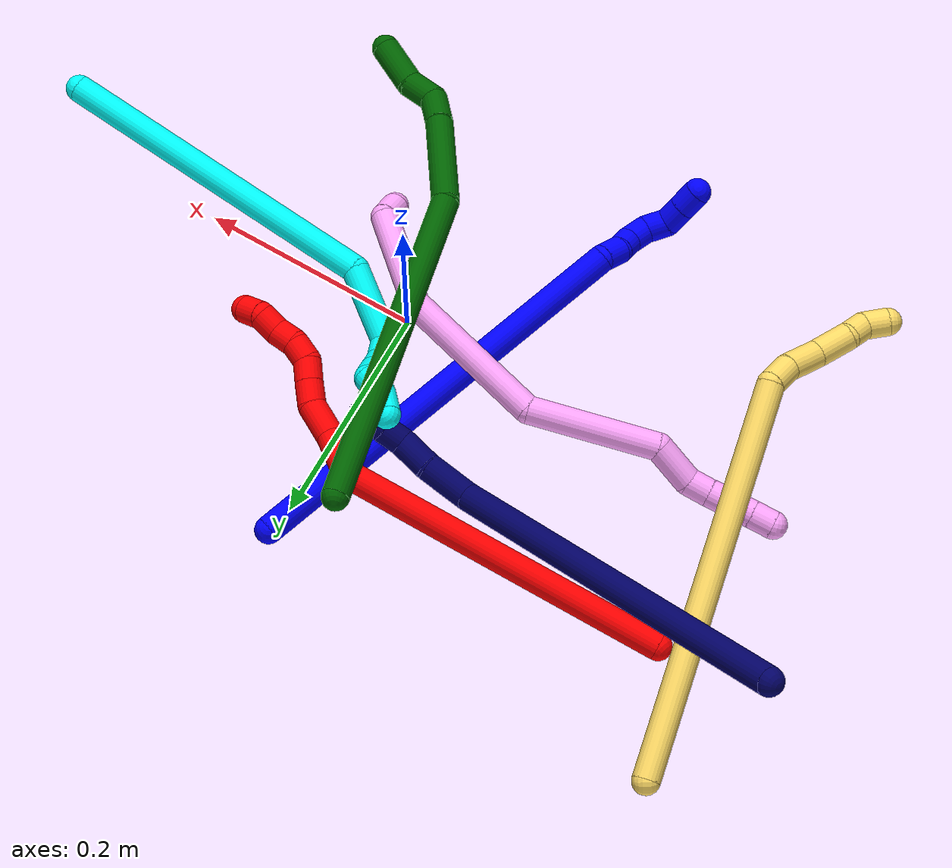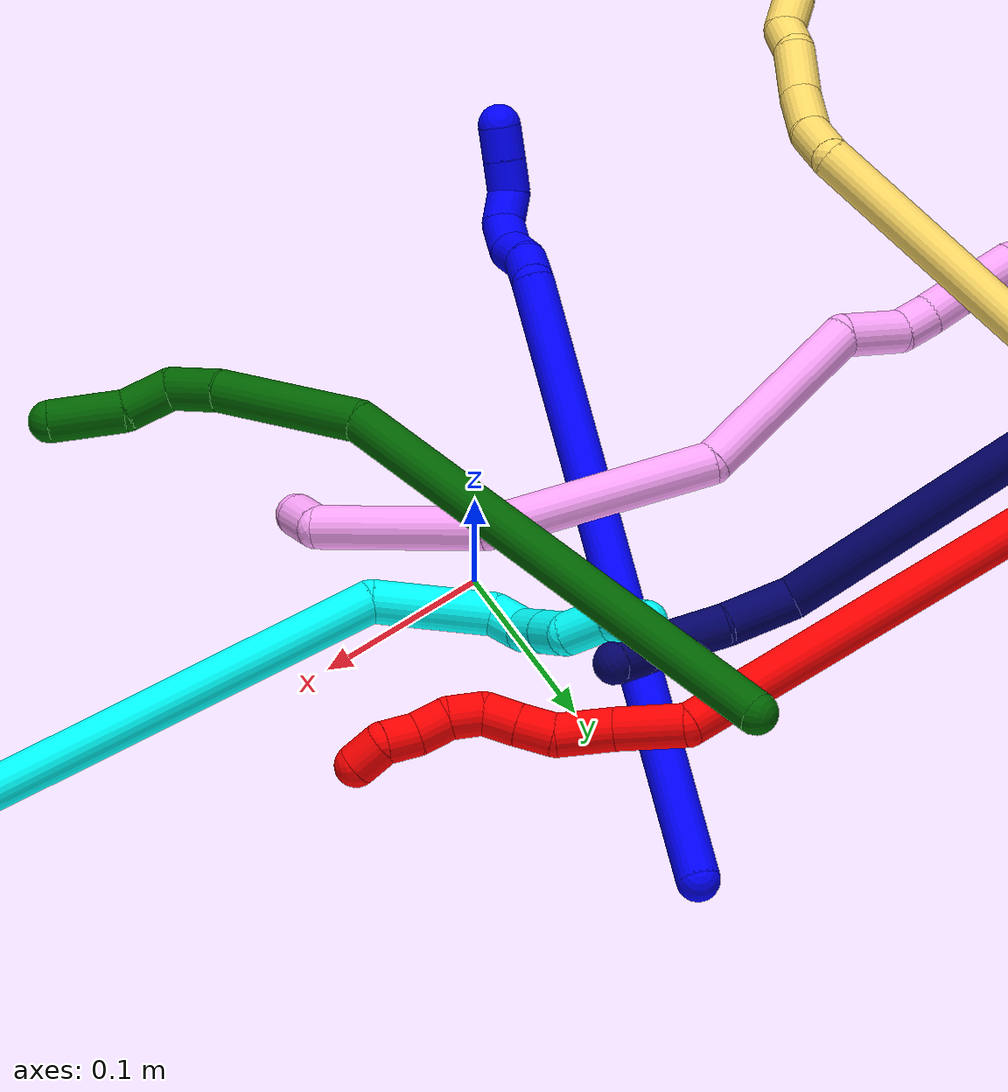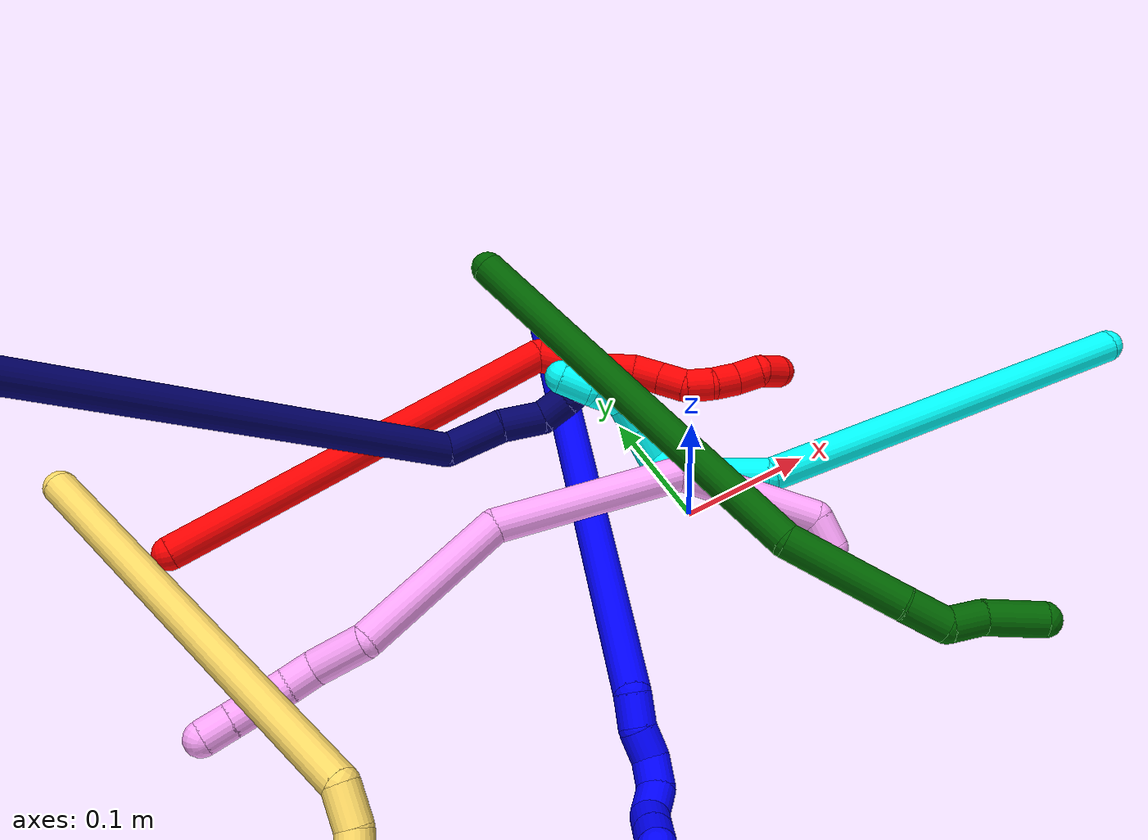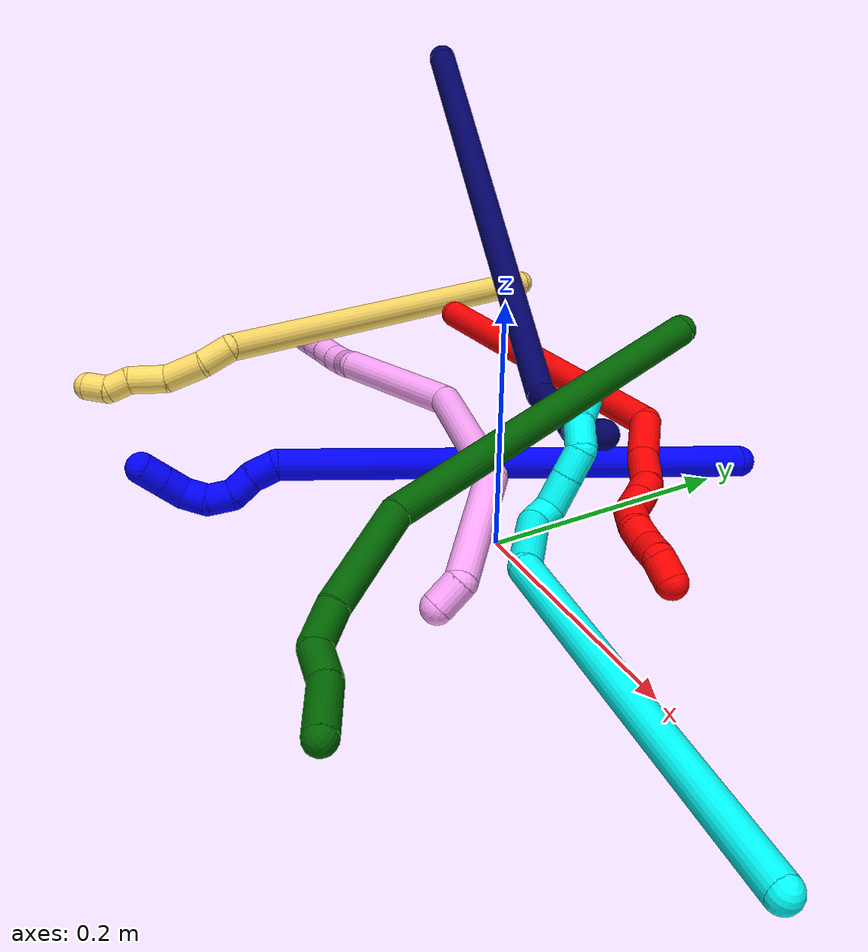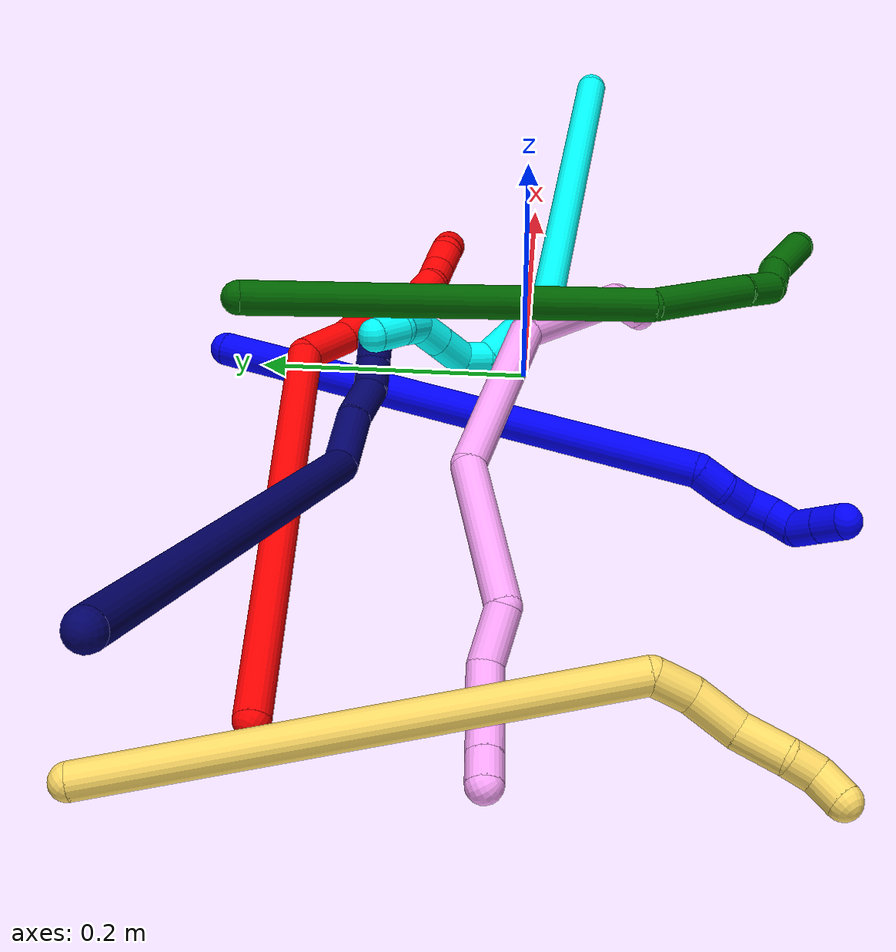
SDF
<sdf version="1.7">
 <world name="default">
  <plugin name="TubeGeneratorPlugin" filename="libtube_generator_plugin.so"/>
  <model name="photoneo_s_sensor">
   <static>1</static>
   <pose>0 0 2 1.57079 1.57079 3.14159</pose>
   <link name="link">
    <inertial><mass>0.1</mass></inertial>
    <sensor name="sensor" type="depth">
     <update_rate>30</update_rate>
     <camera>
      <horizontal_fov>1.22</horizontal_fov>
      <image><width>1920</width><height>1200</height><format>B8G8R8</format></image>
      <clip><near>0.1</near><far>4</far></clip>
      <depth_camera><output>points</output></depth_camera>
     </camera>
     <plugin name="camera_plugin" filename="libgazebo_ros_depth_camera.so">
      <baseline>0.2</baseline>
      <alwaysOn>1</alwaysOn>
      <updateRate>0.0</updateRate>
      <cameraName>camera_ir</cameraName>
      <imageTopicName>/camera/color/image_raw</imageTopicName>
      <cameraInfoTopicName>/camera/color/camera_info</cameraInfoTopicName>
      <depthImageTopicName>/camera/depth/image_raw</depthImageTopicName>
      <depthImageCameraInfoTopicName>/camera/depth/camera_info</depthImageCameraInfoTopicName>
      <pointCloudTopicName>/camera/depth/points</pointCloudTopicName>
      <frameName>fr_optical</frameName>
      <pointCloudCutoff>0.1</pointCloudCutoff>
      <pointCloudCutoffMax>2.0</pointCloudCutoffMax>
      <distortionK1>0</distortionK1>
      <distortionK2>0</distortionK2>
      <distortionK3>0</distortionK3>
      <distortionT1>0</distortionT1>
      <distortionT2>0</distortionT2>
      <CxPrime>0</CxPrime>
      <Cx>0</Cx>
      <Cy>0</Cy>
      <focalLength>0</focalLength>
      <hackBaseline>0</hackBaseline>
     </plugin>
    </sensor>
   </link>
  </model>
  <gravity>0 0 -9.8</gravity>
  <magnetic_field>6e-06 2.3e-05 -4.2e-05</magnetic_field>
  <atmosphere type="adiabatic"/>
  <physics name="default_physics" default="0" type="ode">
   <max_step_size>0.003</max_step_size>
   <real_time_factor>1</real_time_factor>
   <real_time_update_rate>1000</real_time_update_rate>
   <max_contacts>10000</max_contacts>
   <ode>
    <solver>
     <type>quick</type>
     <iters>100</iters>
     <sor>1.3</sor>
     <use_dynamic_moi_rescaling>0</use_dynamic_moi_rescaling>
    </solver>
    <constraints>
     <contact_max_correcting_vel>0</contact_max_correcting_vel>
     <contact_surface_layer>0.001</contact_surface_layer>
     <cfm>0</cfm>
     <erp>0.2</erp>
    </constraints>
   </ode>
  </physics>
  <scene><ambient>0.4 0.4 0.4 1</ambient><background>0.7 0.7 0.7 1</background><shadows>0</shadows></scene>
  <audio><device>default</device></audio>
  <spherical_coordinates>
   <surface_model>EARTH_WGS84</surface_model>
   <latitude_deg>0</latitude_deg>
   <longitude_deg>0</longitude_deg>
   <elevation>0</elevation>
   <heading_deg>0</heading_deg>
  </spherical_coordinates>
  <model name="bin">
   <static>1</static>
   <link name="bottom">
    <collision name="collision-bottom">
     <pose>0 0 -0.01 0 -0 0</pose>
     <geometry><box><size>0.8 0.6 0.02</size></box></geometry>
     <surface>
      <friction><ode><mu>100</mu><mu2>100</mu2></ode></friction>
      <contact><collide_bitmask>65535</collide_bitmask></contact>
     </surface>
    </collision>
   </link>
   <link name="west_wall">
    <collision name="collision-west_wall">
     <pose>-0.41 0 0.1 0 -0 0</pose>
     <geometry><box><size>0.02 0.6 0.2</size></box></geometry>
     <surface>
      <friction><ode><mu>100</mu><mu2>100</mu2></ode></friction>
      <contact><collide_bitmask>65535</collide_bitmask></contact>
     </surface>
    </collision>
   </link>
   <link name="east_wall">
    <collision name="collision-east_wall">
     <pose>0.41 0 0.1 0 -0 0</pose>
     <geometry><box><size>0.02 0.6 0.2</size></box></geometry>
     <surface>
      <friction><ode><mu>100</mu><mu2>100</mu2></ode></friction>
      <contact><collide_bitmask>65535</collide_bitmask></contact>
     </surface>
    </collision>
   </link>
   <link name="south_wall">
    <collision name="collision-south_wall">
     <pose>0 -0.31 0.1 0 -0 0</pose>
     <geometry><box><size>0.8 0.02 0.2</size></box></geometry>
     <surface>
      <friction><ode><mu>100</mu><mu2>100</mu2></ode></friction>
      <contact><collide_bitmask>65535</collide_bitmask></contact>
     </surface>
    </collision>
   </link>
   <link name="north_wall">
    <collision name="collision-north_wall">
     <pose>0 0.31 0.1 0 -0 0</pose>
     <geometry><box><size>0.8 0.02 0.2</size></box></geometry>
     <surface>
      <friction><ode><mu>100</mu><mu2>100</mu2></ode></friction>
      <contact><collide_bitmask>65535</collide_bitmask></contact>
     </surface>
    </collision>
   </link>
  </model>
  <model name="1">
   <static>0</static>
   <link name="1">
    <collision name="collision-cylinder-e_1_1_4">
     <pose>-0.063604 -0.177215 0.011354 1.50682 -0.343937 -0.322988</pose>
     <geometry><cylinder><radius>0.0125</radius><length>0.37725</length></cylinder></geometry>
     <surface>
      <friction><ode><mu>1.16</mu><mu2>1.16</mu2><slip1>0</slip1><slip2>0</slip2></ode></friction>
      <contact><ode><kp>1e+06</kp><kd>1</kd><max_vel>0</max_vel><min_depth>0.001</min_depth></ode></contact>
     </surface>
    </collision>
    <visual name="visual-cylinder-e_1_1_4">
     <pose>-0.063604 -0.177215 0.011354 1.50682 -0.343937 -0.322988</pose>
     <geometry><cylinder><radius>0.0125</radius><length>0.37725</length></cylinder></geometry>
     <material><ambient>0 0 1 1</ambient></material>
    </visual>
    <collision name="collision-cylinder-e_2_4_5">
     <pose>-0.13124 -0.363389 0.017772 2.07433 -0.375602 -0.622423</pose>
     <geometry><cylinder><radius>0.0125</radius><length>0.021989</length></cylinder></geometry>
     <surface>
      <friction><ode><mu>1.16</mu><mu2>1.16</mu2><slip1>0</slip1><slip2>0</slip2></ode></friction>
      <contact><ode><kp>1e+06</kp><kd>1</kd><max_vel>0</max_vel><min_depth>0.001</min_depth></ode></contact>
     </surface>
    </collision>
    <visual name="visual-cylinder-e_2_4_5">
     <pose>-0.13124 -0.363389 0.017772 2.07433 -0.375602 -0.622423</pose>
     <geometry><cylinder><radius>0.0125</radius><length>0.021989</length></cylinder></geometry>
     <material><ambient>0 0 1 1</ambient></material>
    </visual>
    <collision name="collision-cylinder-e_3_5_6">
     <pose>-0.136119 -0.380384 0.006443 2.24277 -0.082175 -0.170057</pose>
     <geometry><cylinder><radius>0.0125</radius><length>0.020608</length></cylinder></geometry>
     <surface>
      <friction><ode><mu>1.16</mu><mu2>1.16</mu2><slip1>0</slip1><slip2>0</slip2></ode></friction>
      <contact><ode><kp>1e+06</kp><kd>1</kd><max_vel>0</max_vel><min_depth>0.001</min_depth></ode></contact>
     </surface>
    </collision>
    <visual name="visual-cylinder-e_3_5_6">
     <pose>-0.136119 -0.380384 0.006443 2.24277 -0.082175 -0.170057</pose>
     <geometry><cylinder><radius>0.0125</radius><length>0.020608</length></cylinder></geometry>
     <material><ambient>0 0 1 1</ambient></material>
    </visual>
    <collision name="collision-cylinder-e_4_6_7">
     <pose>-0.140664 -0.397574 -0.001815 1.77184 -0.377007 -0.458911</pose>
     <geometry><cylinder><radius>0.0125</radius><length>0.020095</length></cylinder></geometry>
     <surface>
      <friction><ode><mu>1.16</mu><mu2>1.16</mu2><slip1>0</slip1><slip2>0</slip2></ode></friction>
      <contact><ode><kp>1e+06</kp><kd>1</kd><max_vel>0</max_vel><min_depth>0.001</min_depth></ode></contact>
     </surface>
    </collision>
    <visual name="visual-cylinder-e_4_6_7">
     <pose>-0.140664 -0.397574 -0.001815 1.77184 -0.377007 -0.458911</pose>
     <geometry><cylinder><radius>0.0125</radius><length>0.020095</length></cylinder></geometry>
     <material><ambient>0 0 1 1</ambient></material>
    </visual>
    <collision name="collision-cylinder-e_5_7_8">
     <pose>-0.151119 -0.413937 -0.002061 1.3499 -0.740662 -0.602538</pose>
     <geometry><cylinder><radius>0.0125</radius><length>0.020025</length></cylinder></geometry>
     <surface>
      <friction><ode><mu>1.16</mu><mu2>1.16</mu2><slip1>0</slip1><slip2>0</slip2></ode></friction>
      <contact><ode><kp>1e+06</kp><kd>1</kd><max_vel>0</max_vel><min_depth>0.001</min_depth></ode></contact>
     </surface>
    </collision>
    <visual name="visual-cylinder-e_5_7_8">
     <pose>-0.151119 -0.413937 -0.002061 1.3499 -0.740662 -0.602538</pose>
     <geometry><cylinder><radius>0.0125</radius><length>0.020025</length></cylinder></geometry>
     <material><ambient>0 0 1 1</ambient></material>
    </visual>
    <collision name="collision-cylinder-e_6_8_9">
     <pose>-0.160692 -0.42861 0.005598 0.890351 -0.285431 -0.136903</pose>
     <geometry><cylinder><radius>0.0125</radius><length>0.020012</length></cylinder></geometry>
     <surface>
      <friction><ode><mu>1.16</mu><mu2>1.16</mu2><slip1>0</slip1><slip2>0</slip2></ode></friction>
      <contact><ode><kp>1e+06</kp><kd>1</kd><max_vel>0</max_vel><min_depth>0.001</min_depth></ode></contact>
     </surface>
    </collision>
    <visual name="visual-cylinder-e_6_8_9">
     <pose>-0.160692 -0.42861 0.005598 0.890351 -0.285431 -0.136903</pose>
     <geometry><cylinder><radius>0.0125</radius><length>0.020012</length></cylinder></geometry>
     <material><ambient>0 0 1 1</ambient></material>
    </visual>
    <collision name="collision-cylinder-e_7_9_2">
     <pose>-0.166262 -0.443554 0.017694 0.89033 -0.278479 -0.133531</pose>
     <geometry><cylinder><radius>0.0125</radius><length>0.020021</length></cylinder></geometry>
     <surface>
      <friction><ode><mu>1.16</mu><mu2>1.16</mu2><slip1>0</slip1><slip2>0</slip2></ode></friction>
      <contact><ode><kp>1e+06</kp><kd>1</kd><max_vel>0</max_vel><min_depth>0.001</min_depth></ode></contact>
     </surface>
    </collision>
    <visual name="visual-cylinder-e_7_9_2">
     <pose>-0.166262 -0.443554 0.017694 0.89033 -0.278479 -0.133531</pose>
     <geometry><cylinder><radius>0.0125</radius><length>0.020021</length></cylinder></geometry>
     <material><ambient>0 0 1 1</ambient></material>
    </visual>
    <collision name="collision-sphere-2">
     <pose>-0.169013 -0.451035 0.02375 0 -0 0</pose>
     <geometry><sphere><radius>0.0125</radius></sphere></geometry>
     <surface>
      <friction><ode><mu>1.16</mu><mu2>1.16</mu2><slip1>0</slip1><slip2>0</slip2></ode></friction>
      <contact><ode><kp>1e+06</kp><kd>1</kd><max_vel>0</max_vel><min_depth>0.001</min_depth></ode></contact>
     </surface>
    </collision>
    <visual name="visual-sphere-2">
     <pose>-0.169013 -0.451035 0.02375 0 -0 0</pose>
     <geometry><sphere><radius>0.0125</radius></sphere></geometry>
     <material><ambient>0 0 1 1</ambient></material>
    </visual>
    <collision name="collision-sphere-9">
     <pose>-0.16351 -0.436073 0.011639 0 -0 0</pose>
     <geometry><sphere><radius>0.0125</radius></sphere></geometry>
     <surface>
      <friction><ode><mu>1.16</mu><mu2>1.16</mu2><slip1>0</slip1><slip2>0</slip2></ode></friction>
      <contact><ode><kp>1e+06</kp><kd>1</kd><max_vel>0</max_vel><min_depth>0.001</min_depth></ode></contact>
     </surface>
    </collision>
    <visual name="visual-sphere-9">
     <pose>-0.16351 -0.436073 0.011639 0 -0 0</pose>
     <geometry><sphere><radius>0.0125</radius></sphere></geometry>
     <material><ambient>0 0 1 1</ambient></material>
    </visual>
    <collision name="collision-sphere-4">
     <pose>-0.127207 -0.35443 0.022707 0 -0 0</pose>
     <geometry><sphere><radius>0.0125</radius></sphere></geometry>
     <surface>
      <friction><ode><mu>1.16</mu><mu2>1.16</mu2><slip1>0</slip1><slip2>0</slip2></ode></friction>
      <contact><ode><kp>1e+06</kp><kd>1</kd><max_vel>0</max_vel><min_depth>0.001</min_depth></ode></contact>
     </surface>
    </collision>
    <visual name="visual-sphere-4">
     <pose>-0.127207 -0.35443 0.022707 0 -0 0</pose>
     <geometry><sphere><radius>0.0125</radius></sphere></geometry>
     <material><ambient>0 0 1 1</ambient></material>
    </visual>
    <collision name="collision-sphere-1">
     <geometry><sphere><radius>0.0125</radius></sphere></geometry>
     <surface>
      <friction><ode><mu>1.16</mu><mu2>1.16</mu2><slip1>0</slip1><slip2>0</slip2></ode></friction>
      <contact><ode><kp>1e+06</kp><kd>1</kd><max_vel>0</max_vel><min_depth>0.001</min_depth></ode></contact>
     </surface>
    </collision>
    <visual name="visual-sphere-1">
     <geometry><sphere><radius>0.0125</radius></sphere></geometry>
     <material><ambient>0 0 1 1</ambient></material>
    </visual>
    <collision name="collision-sphere-8">
     <pose>-0.157875 -0.421147 -0.000442 0 -0 0</pose>
     <geometry><sphere><radius>0.0125</radius></sphere></geometry>
     <surface>
      <friction><ode><mu>1.16</mu><mu2>1.16</mu2><slip1>0</slip1><slip2>0</slip2></ode></friction>
      <contact><ode><kp>1e+06</kp><kd>1</kd><max_vel>0</max_vel><min_depth>0.001</min_depth></ode></contact>
     </surface>
    </collision>
    <visual name="visual-sphere-8">
     <pose>-0.157875 -0.421147 -0.000442 0 -0 0</pose>
     <geometry><sphere><radius>0.0125</radius></sphere></geometry>
     <material><ambient>0 0 1 1</ambient></material>
    </visual>
    <collision name="collision-sphere-5">
     <pose>-0.135274 -0.372347 0.012836 0 -0 0</pose>
     <geometry><sphere><radius>0.0125</radius></sphere></geometry>
     <surface>
      <friction><ode><mu>1.16</mu><mu2>1.16</mu2><slip1>0</slip1><slip2>0</slip2></ode></friction>
      <contact><ode><kp>1e+06</kp><kd>1</kd><max_vel>0</max_vel><min_depth>0.001</min_depth></ode></contact>
     </surface>
    </collision>
    <visual name="visual-sphere-5">
     <pose>-0.135274 -0.372347 0.012836 0 -0 0</pose>
     <geometry><sphere><radius>0.0125</radius></sphere></geometry>
     <material><ambient>0 0 1 1</ambient></material>
    </visual>
    <collision name="collision-sphere-6">
     <pose>-0.136965 -0.38842 5.1e-05 0 -0 0</pose>
     <geometry><sphere><radius>0.0125</radius></sphere></geometry>
     <surface>
      <friction><ode><mu>1.16</mu><mu2>1.16</mu2><slip1>0</slip1><slip2>0</slip2></ode></friction>
      <contact><ode><kp>1e+06</kp><kd>1</kd><max_vel>0</max_vel><min_depth>0.001</min_depth></ode></contact>
     </surface>
    </collision>
    <visual name="visual-sphere-6">
     <pose>-0.136965 -0.38842 5.1e-05 0 -0 0</pose>
     <geometry><sphere><radius>0.0125</radius></sphere></geometry>
     <material><ambient>0 0 1 1</ambient></material>
    </visual>
    <collision name="collision-sphere-7">
     <pose>-0.144363 -0.406728 -0.00368 0 -0 0</pose>
     <geometry><sphere><radius>0.0125</radius></sphere></geometry>
     <surface>
      <friction><ode><mu>1.16</mu><mu2>1.16</mu2><slip1>0</slip1><slip2>0</slip2></ode></friction>
      <contact><ode><kp>1e+06</kp><kd>1</kd><max_vel>0</max_vel><min_depth>0.001</min_depth></ode></contact>
     </surface>
    </collision>
    <visual name="visual-sphere-7">
     <pose>-0.144363 -0.406728 -0.00368 0 -0 0</pose>
     <geometry><sphere><radius>0.0125</radius></sphere></geometry>
     <material><ambient>0 0 1 1</ambient></material>
    </visual>
    <inertial>
     <pose>-0.084165 -0.23284 0.01039 0 -0 0</pose>
     <mass>0.5</mass>
     <inertia>
      <ixx>0.002658</ixx>
      <ixy>0</ixy>
      <ixz>0</ixz>
      <iyy>-0.000626</iyy>
      <iyz>0</iyz>
      <izz>0.005743</izz>
     </inertia>
    </inertial>
   </link>
   <pose>0.004148 0.227844 0.011486 -0.033946 -0.06999 0.000722</pose>
  </model>
  <model name="2">
   <static>0</static>
   <link name="2">
    <collision name="collision-cylinder-e_1_1_4">
     <pose>-0.047955 -0.00534 -0.143271 3.10434 -0.322783 -2.91372</pose>
     <geometry><cylinder><radius>0.0125</radius><length>0.302355</length></cylinder></geometry>
     <surface>
      <friction><ode><mu>1.16</mu><mu2>1.16</mu2><slip1>0</slip1><slip2>0</slip2></ode></friction>
      <contact><ode><kp>1e+06</kp><kd>1</kd><max_vel>0</max_vel><min_depth>0.001</min_depth></ode></contact>
     </surface>
    </collision>
    <visual name="visual-cylinder-e_1_1_4">
     <pose>-0.047955 -0.00534 -0.143271 3.10434 -0.322783 -2.91372</pose>
     <geometry><cylinder><radius>0.0125</radius><length>0.302355</length></cylinder></geometry>
     <material><ambient>1 0 0 1</ambient></material>
    </visual>
    <collision name="collision-cylinder-e_2_4_5">
     <pose>-0.087491 -0.01514 -0.305141 2.90628 0.414626 2.11762</pose>
     <geometry><cylinder><radius>0.0125</radius><length>0.041794</length></cylinder></geometry>
     <surface>
      <friction><ode><mu>1.16</mu><mu2>1.16</mu2><slip1>0</slip1><slip2>0</slip2></ode></friction>
      <contact><ode><kp>1e+06</kp><kd>1</kd><max_vel>0</max_vel><min_depth>0.001</min_depth></ode></contact>
     </surface>
    </collision>
    <visual name="visual-cylinder-e_2_4_5">
     <pose>-0.087491 -0.01514 -0.305141 2.90628 0.414626 2.11762</pose>
     <geometry><cylinder><radius>0.0125</radius><length>0.041794</length></cylinder></geometry>
     <material><ambient>1 0 0 1</ambient></material>
    </visual>
    <collision name="collision-cylinder-e_3_5_6">
     <pose>-0.074855 -0.021192 -0.339826 3.04288 0.255223 2.40659</pose>
     <geometry><cylinder><radius>0.0125</radius><length>0.03341</length></cylinder></geometry>
     <surface>
      <friction><ode><mu>1.16</mu><mu2>1.16</mu2><slip1>0</slip1><slip2>0</slip2></ode></friction>
      <contact><ode><kp>1e+06</kp><kd>1</kd><max_vel>0</max_vel><min_depth>0.001</min_depth></ode></contact>
     </surface>
    </collision>
    <visual name="visual-cylinder-e_3_5_6">
     <pose>-0.074855 -0.021192 -0.339826 3.04288 0.255223 2.40659</pose>
     <geometry><cylinder><radius>0.0125</radius><length>0.03341</length></cylinder></geometry>
     <material><ambient>1 0 0 1</ambient></material>
    </visual>
    <collision name="collision-cylinder-e_4_6_7">
     <pose>-0.064408 -0.022021 -0.364804 -3.05584 0.609384 -2.87042</pose>
     <geometry><cylinder><radius>0.0125</radius><length>0.02177</length></cylinder></geometry>
     <surface>
      <friction><ode><mu>1.16</mu><mu2>1.16</mu2><slip1>0</slip1><slip2>0</slip2></ode></friction>
      <contact><ode><kp>1e+06</kp><kd>1</kd><max_vel>0</max_vel><min_depth>0.001</min_depth></ode></contact>
     </surface>
    </collision>
    <visual name="visual-cylinder-e_4_6_7">
     <pose>-0.064408 -0.022021 -0.364804 -3.05584 0.609384 -2.87042</pose>
     <geometry><cylinder><radius>0.0125</radius><length>0.02177</length></cylinder></geometry>
     <material><ambient>1 0 0 1</ambient></material>
    </visual>
    <collision name="collision-cylinder-e_5_7_8">
     <pose>-0.052042 -0.020217 -0.381906 -3.01564 0.637981 -2.76428</pose>
     <geometry><cylinder><radius>0.0125</radius><length>0.020602</length></cylinder></geometry>
     <surface>
      <friction><ode><mu>1.16</mu><mu2>1.16</mu2><slip1>0</slip1><slip2>0</slip2></ode></friction>
      <contact><ode><kp>1e+06</kp><kd>1</kd><max_vel>0</max_vel><min_depth>0.001</min_depth></ode></contact>
     </surface>
    </collision>
    <visual name="visual-cylinder-e_5_7_8">
     <pose>-0.052042 -0.020217 -0.381906 -3.01564 0.637981 -2.76428</pose>
     <geometry><cylinder><radius>0.0125</radius><length>0.020602</length></cylinder></geometry>
     <material><ambient>1 0 0 1</ambient></material>
    </visual>
    <collision name="collision-cylinder-e_6_8_9">
     <pose>-0.044302 -0.019371 -0.399995 3.12199 0.161008 2.89982</pose>
     <geometry><cylinder><radius>0.0125</radius><length>0.020022</length></cylinder></geometry>
     <surface>
      <friction><ode><mu>1.16</mu><mu2>1.16</mu2><slip1>0</slip1><slip2>0</slip2></ode></friction>
      <contact><ode><kp>1e+06</kp><kd>1</kd><max_vel>0</max_vel><min_depth>0.001</min_depth></ode></contact>
     </surface>
    </collision>
    <visual name="visual-cylinder-e_6_8_9">
     <pose>-0.044302 -0.019371 -0.399995 3.12199 0.161008 2.89982</pose>
     <geometry><cylinder><radius>0.0125</radius><length>0.020022</length></cylinder></geometry>
     <material><ambient>1 0 0 1</ambient></material>
    </visual>
    <collision name="collision-cylinder-e_7_9_10">
     <pose>-0.043679 -0.021997 -0.419546 2.89526 -0.098076 -0.754889</pose>
     <geometry><cylinder><radius>0.0125</radius><length>0.020042</length></cylinder></geometry>
     <surface>
      <friction><ode><mu>1.16</mu><mu2>1.16</mu2><slip1>0</slip1><slip2>0</slip2></ode></friction>
      <contact><ode><kp>1e+06</kp><kd>1</kd><max_vel>0</max_vel><min_depth>0.001</min_depth></ode></contact>
     </surface>
    </collision>
    <visual name="visual-cylinder-e_7_9_10">
     <pose>-0.043679 -0.021997 -0.419546 2.89526 -0.098076 -0.754889</pose>
     <geometry><cylinder><radius>0.0125</radius><length>0.020042</length></cylinder></geometry>
     <material><ambient>1 0 0 1</ambient></material>
    </visual>
    <collision name="collision-cylinder-e_8_10_11">
     <pose>-0.045313 -0.023773 -0.439177 -3.0759 -0.065297 1.56476</pose>
     <geometry><cylinder><radius>0.0125</radius><length>0.020004</length></cylinder></geometry>
     <surface>
      <friction><ode><mu>1.16</mu><mu2>1.16</mu2><slip1>0</slip1><slip2>0</slip2></ode></friction>
      <contact><ode><kp>1e+06</kp><kd>1</kd><max_vel>0</max_vel><min_depth>0.001</min_depth></ode></contact>
     </surface>
    </collision>
    <visual name="visual-cylinder-e_8_10_11">
     <pose>-0.045313 -0.023773 -0.439177 -3.0759 -0.065297 1.56476</pose>
     <geometry><cylinder><radius>0.0125</radius><length>0.020004</length></cylinder></geometry>
     <material><ambient>1 0 0 1</ambient></material>
    </visual>
    <collision name="collision-cylinder-e_9_11_2">
     <pose>-0.046857 -0.028746 -0.457354 2.54108 -0.089302 -0.286642</pose>
     <geometry><cylinder><radius>0.0125</radius><length>0.02</length></cylinder></geometry>
     <surface>
      <friction><ode><mu>1.16</mu><mu2>1.16</mu2><slip1>0</slip1><slip2>0</slip2></ode></friction>
      <contact><ode><kp>1e+06</kp><kd>1</kd><max_vel>0</max_vel><min_depth>0.001</min_depth></ode></contact>
     </surface>
    </collision>
    <visual name="visual-cylinder-e_9_11_2">
     <pose>-0.046857 -0.028746 -0.457354 2.54108 -0.089302 -0.286642</pose>
     <geometry><cylinder><radius>0.0125</radius><length>0.02</length></cylinder></geometry>
     <material><ambient>1 0 0 1</ambient></material>
    </visual>
    <collision name="collision-sphere-2">
     <pose>-0.047749 -0.034374 -0.465572 0 -0 0</pose>
     <geometry><sphere><radius>0.0125</radius></sphere></geometry>
     <surface>
      <friction><ode><mu>1.16</mu><mu2>1.16</mu2><slip1>0</slip1><slip2>0</slip2></ode></friction>
      <contact><ode><kp>1e+06</kp><kd>1</kd><max_vel>0</max_vel><min_depth>0.001</min_depth></ode></contact>
     </surface>
    </collision>
    <visual name="visual-sphere-2">
     <pose>-0.047749 -0.034374 -0.465572 0 -0 0</pose>
     <geometry><sphere><radius>0.0125</radius></sphere></geometry>
     <material><ambient>1 0 0 1</ambient></material>
    </visual>
    <collision name="collision-sphere-11">
     <pose>-0.045965 -0.023118 -0.449136 0 -0 0</pose>
     <geometry><sphere><radius>0.0125</radius></sphere></geometry>
     <surface>
      <friction><ode><mu>1.16</mu><mu2>1.16</mu2><slip1>0</slip1><slip2>0</slip2></ode></friction>
      <contact><ode><kp>1e+06</kp><kd>1</kd><max_vel>0</max_vel><min_depth>0.001</min_depth></ode></contact>
     </surface>
    </collision>
    <visual name="visual-sphere-11">
     <pose>-0.045965 -0.023118 -0.449136 0 -0 0</pose>
     <geometry><sphere><radius>0.0125</radius></sphere></geometry>
     <material><ambient>1 0 0 1</ambient></material>
    </visual>
    <collision name="collision-sphere-10">
     <pose>-0.04466 -0.024428 -0.429218 0 -0 0</pose>
     <geometry><sphere><radius>0.0125</radius></sphere></geometry>
     <surface>
      <friction><ode><mu>1.16</mu><mu2>1.16</mu2><slip1>0</slip1><slip2>0</slip2></ode></friction>
      <contact><ode><kp>1e+06</kp><kd>1</kd><max_vel>0</max_vel><min_depth>0.001</min_depth></ode></contact>
     </surface>
    </collision>
    <visual name="visual-sphere-10">
     <pose>-0.04466 -0.024428 -0.429218 0 -0 0</pose>
     <geometry><sphere><radius>0.0125</radius></sphere></geometry>
     <material><ambient>1 0 0 1</ambient></material>
    </visual>
    <collision name="collision-sphere-9">
     <pose>-0.042698 -0.019565 -0.409874 0 -0 0</pose>
     <geometry><sphere><radius>0.0125</radius></sphere></geometry>
     <surface>
      <friction><ode><mu>1.16</mu><mu2>1.16</mu2><slip1>0</slip1><slip2>0</slip2></ode></friction>
      <contact><ode><kp>1e+06</kp><kd>1</kd><max_vel>0</max_vel><min_depth>0.001</min_depth></ode></contact>
     </surface>
    </collision>
    <visual name="visual-sphere-9">
     <pose>-0.042698 -0.019565 -0.409874 0 -0 0</pose>
     <geometry><sphere><radius>0.0125</radius></sphere></geometry>
     <material><ambient>1 0 0 1</ambient></material>
    </visual>
    <collision name="collision-sphere-4">
     <pose>-0.095909 -0.010681 -0.286542 0 -0 0</pose>
     <geometry><sphere><radius>0.0125</radius></sphere></geometry>
     <surface>
      <friction><ode><mu>1.16</mu><mu2>1.16</mu2><slip1>0</slip1><slip2>0</slip2></ode></friction>
      <contact><ode><kp>1e+06</kp><kd>1</kd><max_vel>0</max_vel><min_depth>0.001</min_depth></ode></contact>
     </surface>
    </collision>
    <visual name="visual-sphere-4">
     <pose>-0.095909 -0.010681 -0.286542 0 -0 0</pose>
     <geometry><sphere><radius>0.0125</radius></sphere></geometry>
     <material><ambient>1 0 0 1</ambient></material>
    </visual>
    <collision name="collision-sphere-1">
     <geometry><sphere><radius>0.0125</radius></sphere></geometry>
     <surface>
      <friction><ode><mu>1.16</mu><mu2>1.16</mu2><slip1>0</slip1><slip2>0</slip2></ode></friction>
      <contact><ode><kp>1e+06</kp><kd>1</kd><max_vel>0</max_vel><min_depth>0.001</min_depth></ode></contact>
     </surface>
    </collision>
    <visual name="visual-sphere-1">
     <geometry><sphere><radius>0.0125</radius></sphere></geometry>
     <material><ambient>1 0 0 1</ambient></material>
    </visual>
    <collision name="collision-sphere-8">
     <pose>-0.045907 -0.019177 -0.390115 0 -0 0</pose>
     <geometry><sphere><radius>0.0125</radius></sphere></geometry>
     <surface>
      <friction><ode><mu>1.16</mu><mu2>1.16</mu2><slip1>0</slip1><slip2>0</slip2></ode></friction>
      <contact><ode><kp>1e+06</kp><kd>1</kd><max_vel>0</max_vel><min_depth>0.001</min_depth></ode></contact>
     </surface>
    </collision>
    <visual name="visual-sphere-8">
     <pose>-0.045907 -0.019177 -0.390115 0 -0 0</pose>
     <geometry><sphere><radius>0.0125</radius></sphere></geometry>
     <material><ambient>1 0 0 1</ambient></material>
    </visual>
    <collision name="collision-sphere-5">
     <pose>-0.079073 -0.019599 -0.323741 0 -0 0</pose>
     <geometry><sphere><radius>0.0125</radius></sphere></geometry>
     <surface>
      <friction><ode><mu>1.16</mu><mu2>1.16</mu2><slip1>0</slip1><slip2>0</slip2></ode></friction>
      <contact><ode><kp>1e+06</kp><kd>1</kd><max_vel>0</max_vel><min_depth>0.001</min_depth></ode></contact>
     </surface>
    </collision>
    <visual name="visual-sphere-5">
     <pose>-0.079073 -0.019599 -0.323741 0 -0 0</pose>
     <geometry><sphere><radius>0.0125</radius></sphere></geometry>
     <material><ambient>1 0 0 1</ambient></material>
    </visual>
    <collision name="collision-sphere-6">
     <pose>-0.070638 -0.022785 -0.355911 0 -0 0</pose>
     <geometry><sphere><radius>0.0125</radius></sphere></geometry>
     <surface>
      <friction><ode><mu>1.16</mu><mu2>1.16</mu2><slip1>0</slip1><slip2>0</slip2></ode></friction>
      <contact><ode><kp>1e+06</kp><kd>1</kd><max_vel>0</max_vel><min_depth>0.001</min_depth></ode></contact>
     </surface>
    </collision>
    <visual name="visual-sphere-6">
     <pose>-0.070638 -0.022785 -0.355911 0 -0 0</pose>
     <geometry><sphere><radius>0.0125</radius></sphere></geometry>
     <material><ambient>1 0 0 1</ambient></material>
    </visual>
    <collision name="collision-sphere-7">
     <pose>-0.058178 -0.021256 -0.373697 0 -0 0</pose>
     <geometry><sphere><radius>0.0125</radius></sphere></geometry>
     <surface>
      <friction><ode><mu>1.16</mu><mu2>1.16</mu2><slip1>0</slip1><slip2>0</slip2></ode></friction>
      <contact><ode><kp>1e+06</kp><kd>1</kd><max_vel>0</max_vel><min_depth>0.001</min_depth></ode></contact>
     </surface>
    </collision>
    <visual name="visual-sphere-7">
     <pose>-0.058178 -0.021256 -0.373697 0 -0 0</pose>
     <geometry><sphere><radius>0.0125</radius></sphere></geometry>
     <material><ambient>1 0 0 1</ambient></material>
    </visual>
    <inertial>
     <pose>-0.053475 -0.011461 -0.23517 0 -0 0</pose>
     <mass>0.5</mass>
     <inertia>
      <ixx>-0.002638</ixx>
      <ixy>0</ixy>
      <ixz>0</ixz>
      <iyy>0.00178</iyy>
      <iyz>0</iyz>
      <izz>0.000777</izz>
     </inertia>
    </inertial>
   </link>
   <pose>-0.33629 0.153058 0.019362 1.62348 0.239441 -1.85914</pose>
  </model>
  <model name="3">
   <static>0</static>
   <link name="3">
    <collision name="collision-cylinder-e_1_1_4">
     <pose>-0.145979 -0.026583 -0.042657 2.58431 -1.2392 -2.37874</pose>
     <geometry><cylinder><radius>0.0125</radius><length>0.308779</length></cylinder></geometry>
     <surface>
      <friction><ode><mu>1.16</mu><mu2>1.16</mu2><slip1>0</slip1><slip2>0</slip2></ode></friction>
      <contact><ode><kp>1e+06</kp><kd>1</kd><max_vel>0</max_vel><min_depth>0.001</min_depth></ode></contact>
     </surface>
    </collision>
    <visual name="visual-cylinder-e_1_1_4">
     <pose>-0.145979 -0.026583 -0.042657 2.58431 -1.2392 -2.37874</pose>
     <geometry><cylinder><radius>0.0125</radius><length>0.308779</length></cylinder></geometry>
     <material><ambient>0.003922 1 0.996078 1</ambient></material>
    </visual>
    <collision name="collision-cylinder-e_2_4_5">
     <pose>-0.322774 -0.039385 -0.095449 -2.20491 -1.06407 1.72175</pose>
     <geometry><cylinder><radius>0.0125</radius><length>0.070491</length></cylinder></geometry>
     <surface>
      <friction><ode><mu>1.16</mu><mu2>1.16</mu2><slip1>0</slip1><slip2>0</slip2></ode></friction>
      <contact><ode><kp>1e+06</kp><kd>1</kd><max_vel>0</max_vel><min_depth>0.001</min_depth></ode></contact>
     </surface>
    </collision>
    <visual name="visual-cylinder-e_2_4_5">
     <pose>-0.322774 -0.039385 -0.095449 -2.20491 -1.06407 1.72175</pose>
     <geometry><cylinder><radius>0.0125</radius><length>0.070491</length></cylinder></geometry>
     <material><ambient>0.003922 1 0.996078 1</ambient></material>
    </visual>
    <collision name="collision-cylinder-e_3_5_6">
     <pose>-0.360005 -0.017879 -0.103551 -1.31365 -0.67647 0.529683</pose>
     <geometry><cylinder><radius>0.0125</radius><length>0.02049</length></cylinder></geometry>
     <surface>
      <friction><ode><mu>1.16</mu><mu2>1.16</mu2><slip1>0</slip1><slip2>0</slip2></ode></friction>
      <contact><ode><kp>1e+06</kp><kd>1</kd><max_vel>0</max_vel><min_depth>0.001</min_depth></ode></contact>
     </surface>
    </collision>
    <visual name="visual-cylinder-e_3_5_6">
     <pose>-0.360005 -0.017879 -0.103551 -1.31365 -0.67647 0.529683</pose>
     <geometry><cylinder><radius>0.0125</radius><length>0.02049</length></cylinder></geometry>
     <material><ambient>0.003922 1 0.996078 1</ambient></material>
    </visual>
    <collision name="collision-cylinder-e_4_6_7">
     <pose>-0.373763 -0.004726 -0.091274 -0.487103 -0.564692 0.14392</pose>
     <geometry><cylinder><radius>0.0125</radius><length>0.02745</length></cylinder></geometry>
     <surface>
      <friction><ode><mu>1.16</mu><mu2>1.16</mu2><slip1>0</slip1><slip2>0</slip2></ode></friction>
      <contact><ode><kp>1e+06</kp><kd>1</kd><max_vel>0</max_vel><min_depth>0.001</min_depth></ode></contact>
     </surface>
    </collision>
    <visual name="visual-cylinder-e_4_6_7">
     <pose>-0.373763 -0.004726 -0.091274 -0.487103 -0.564692 0.14392</pose>
     <geometry><cylinder><radius>0.0125</radius><length>0.02745</length></cylinder></geometry>
     <material><ambient>0.003922 1 0.996078 1</ambient></material>
    </visual>
    <collision name="collision-cylinder-e_5_7_8">
     <pose>-0.387314 0.005401 -0.072503 -0.503904 -0.567521 0.149863</pose>
     <geometry><cylinder><radius>0.0125</radius><length>0.023091</length></cylinder></geometry>
     <surface>
      <friction><ode><mu>1.16</mu><mu2>1.16</mu2><slip1>0</slip1><slip2>0</slip2></ode></friction>
      <contact><ode><kp>1e+06</kp><kd>1</kd><max_vel>0</max_vel><min_depth>0.001</min_depth></ode></contact>
     </surface>
    </collision>
    <visual name="visual-cylinder-e_5_7_8">
     <pose>-0.387314 0.005401 -0.072503 -0.503904 -0.567521 0.149863</pose>
     <geometry><cylinder><radius>0.0125</radius><length>0.023091</length></cylinder></geometry>
     <material><ambient>0.003922 1 0.996078 1</ambient></material>
    </visual>
    <collision name="collision-cylinder-e_6_8_9">
     <pose>-0.405906 0.011002 -0.059776 -0.211076 -1.23687 0.150467</pose>
     <geometry><cylinder><radius>0.0125</radius><length>0.02622</length></cylinder></geometry>
     <surface>
      <friction><ode><mu>1.16</mu><mu2>1.16</mu2><slip1>0</slip1><slip2>0</slip2></ode></friction>
      <contact><ode><kp>1e+06</kp><kd>1</kd><max_vel>0</max_vel><min_depth>0.001</min_depth></ode></contact>
     </surface>
    </collision>
    <visual name="visual-cylinder-e_6_8_9">
     <pose>-0.405906 0.011002 -0.059776 -0.211076 -1.23687 0.150467</pose>
     <geometry><cylinder><radius>0.0125</radius><length>0.02622</length></cylinder></geometry>
     <material><ambient>0.003922 1 0.996078 1</ambient></material>
    </visual>
    <collision name="collision-cylinder-e_7_9_2">
     <pose>-0.428608 0.017262 -0.053937 -1.27414 -1.07316 0.829256</pose>
     <geometry><cylinder><radius>0.0125</radius><length>0.02348</length></cylinder></geometry>
     <surface>
      <friction><ode><mu>1.16</mu><mu2>1.16</mu2><slip1>0</slip1><slip2>0</slip2></ode></friction>
      <contact><ode><kp>1e+06</kp><kd>1</kd><max_vel>0</max_vel><min_depth>0.001</min_depth></ode></contact>
     </surface>
    </collision>
    <visual name="visual-cylinder-e_7_9_2">
     <pose>-0.428608 0.017262 -0.053937 -1.27414 -1.07316 0.829256</pose>
     <geometry><cylinder><radius>0.0125</radius><length>0.02348</length></cylinder></geometry>
     <material><ambient>0.003922 1 0.996078 1</ambient></material>
    </visual>
    <collision name="collision-sphere-2">
     <pose>-0.438924 0.022621 -0.052299 0 -0 0</pose>
     <geometry><sphere><radius>0.0125</radius></sphere></geometry>
     <surface>
      <friction><ode><mu>1.16</mu><mu2>1.16</mu2><slip1>0</slip1><slip2>0</slip2></ode></friction>
      <contact><ode><kp>1e+06</kp><kd>1</kd><max_vel>0</max_vel><min_depth>0.001</min_depth></ode></contact>
     </surface>
    </collision>
    <visual name="visual-sphere-2">
     <pose>-0.438924 0.022621 -0.052299 0 -0 0</pose>
     <geometry><sphere><radius>0.0125</radius></sphere></geometry>
     <material><ambient>0.003922 1 0.996078 1</ambient></material>
    </visual>
    <collision name="collision-sphere-9">
     <pose>-0.418292 0.011903 -0.055575 0 -0 0</pose>
     <geometry><sphere><radius>0.0125</radius></sphere></geometry>
     <surface>
      <friction><ode><mu>1.16</mu><mu2>1.16</mu2><slip1>0</slip1><slip2>0</slip2></ode></friction>
      <contact><ode><kp>1e+06</kp><kd>1</kd><max_vel>0</max_vel><min_depth>0.001</min_depth></ode></contact>
     </surface>
    </collision>
    <visual name="visual-sphere-9">
     <pose>-0.418292 0.011903 -0.055575 0 -0 0</pose>
     <geometry><sphere><radius>0.0125</radius></sphere></geometry>
     <material><ambient>0.003922 1 0.996078 1</ambient></material>
    </visual>
    <collision name="collision-sphere-4">
     <pose>-0.291958 -0.053165 -0.085315 0 -0 0</pose>
     <geometry><sphere><radius>0.0125</radius></sphere></geometry>
     <surface>
      <friction><ode><mu>1.16</mu><mu2>1.16</mu2><slip1>0</slip1><slip2>0</slip2></ode></friction>
      <contact><ode><kp>1e+06</kp><kd>1</kd><max_vel>0</max_vel><min_depth>0.001</min_depth></ode></contact>
     </surface>
    </collision>
    <visual name="visual-sphere-4">
     <pose>-0.291958 -0.053165 -0.085315 0 -0 0</pose>
     <geometry><sphere><radius>0.0125</radius></sphere></geometry>
     <material><ambient>0.003922 1 0.996078 1</ambient></material>
    </visual>
    <collision name="collision-sphere-1">
     <geometry><sphere><radius>0.0125</radius></sphere></geometry>
     <surface>
      <friction><ode><mu>1.16</mu><mu2>1.16</mu2><slip1>0</slip1><slip2>0</slip2></ode></friction>
      <contact><ode><kp>1e+06</kp><kd>1</kd><max_vel>0</max_vel><min_depth>0.001</min_depth></ode></contact>
     </surface>
    </collision>
    <visual name="visual-sphere-1">
     <geometry><sphere><radius>0.0125</radius></sphere></geometry>
     <material><ambient>0.003922 1 0.996078 1</ambient></material>
    </visual>
    <collision name="collision-sphere-8">
     <pose>-0.393521 0.010102 -0.063978 0 -0 0</pose>
     <geometry><sphere><radius>0.0125</radius></sphere></geometry>
     <surface>
      <friction><ode><mu>1.16</mu><mu2>1.16</mu2><slip1>0</slip1><slip2>0</slip2></ode></friction>
      <contact><ode><kp>1e+06</kp><kd>1</kd><max_vel>0</max_vel><min_depth>0.001</min_depth></ode></contact>
     </surface>
    </collision>
    <visual name="visual-sphere-8">
     <pose>-0.393521 0.010102 -0.063978 0 -0 0</pose>
     <geometry><sphere><radius>0.0125</radius></sphere></geometry>
     <material><ambient>0.003922 1 0.996078 1</ambient></material>
    </visual>
    <collision name="collision-sphere-5">
     <pose>-0.353591 -0.025605 -0.105583 0 -0 0</pose>
     <geometry><sphere><radius>0.0125</radius></sphere></geometry>
     <surface>
      <friction><ode><mu>1.16</mu><mu2>1.16</mu2><slip1>0</slip1><slip2>0</slip2></ode></friction>
      <contact><ode><kp>1e+06</kp><kd>1</kd><max_vel>0</max_vel><min_depth>0.001</min_depth></ode></contact>
     </surface>
    </collision>
    <visual name="visual-sphere-5">
     <pose>-0.353591 -0.025605 -0.105583 0 -0 0</pose>
     <geometry><sphere><radius>0.0125</radius></sphere></geometry>
     <material><ambient>0.003922 1 0.996078 1</ambient></material>
    </visual>
    <collision name="collision-sphere-6">
     <pose>-0.366419 -0.010153 -0.10152 0 -0 0</pose>
     <geometry><sphere><radius>0.0125</radius></sphere></geometry>
     <surface>
      <friction><ode><mu>1.16</mu><mu2>1.16</mu2><slip1>0</slip1><slip2>0</slip2></ode></friction>
      <contact><ode><kp>1e+06</kp><kd>1</kd><max_vel>0</max_vel><min_depth>0.001</min_depth></ode></contact>
     </surface>
    </collision>
    <visual name="visual-sphere-6">
     <pose>-0.366419 -0.010153 -0.10152 0 -0 0</pose>
     <geometry><sphere><radius>0.0125</radius></sphere></geometry>
     <material><ambient>0.003922 1 0.996078 1</ambient></material>
    </visual>
    <collision name="collision-sphere-7">
     <pose>-0.381108 0.000701 -0.081029 0 -0 0</pose>
     <geometry><sphere><radius>0.0125</radius></sphere></geometry>
     <surface>
      <friction><ode><mu>1.16</mu><mu2>1.16</mu2><slip1>0</slip1><slip2>0</slip2></ode></friction>
      <contact><ode><kp>1e+06</kp><kd>1</kd><max_vel>0</max_vel><min_depth>0.001</min_depth></ode></contact>
     </surface>
    </collision>
    <visual name="visual-sphere-7">
     <pose>-0.381108 0.000701 -0.081029 0 -0 0</pose>
     <geometry><sphere><radius>0.0125</radius></sphere></geometry>
     <material><ambient>0.003922 1 0.996078 1</ambient></material>
    </visual>
    <inertial>
     <pose>-0.230228 -0.021324 -0.05807 0 -0 0</pose>
     <mass>0.5</mass>
     <inertia>
      <ixx>-0.001148</ixx>
      <ixy>0</ixy>
      <ixz>0</ixz>
      <iyy>0.001863</iyy>
      <iyz>0</iyz>
      <izz>0.00277</izz>
     </inertia>
    </inertial>
   </link>
   <pose>0.368591 -0.04342 0.012256 -0.201568 0.271004 -0.321106</pose>
  </model>
  <model name="4">
   <static>0</static>
   <link name="4">
    <collision name="collision-cylinder-e_1_1_4">
     <pose>0.002291 0.010819 -0.004676 -1.9788 0.191964 -0.290938</pose>
     <geometry><cylinder><radius>0.0125</radius><length>0.024014</length></cylinder></geometry>
     <surface>
      <friction><ode><mu>1.16</mu><mu2>1.16</mu2><slip1>0</slip1><slip2>0</slip2></ode></friction>
      <contact><ode><kp>1e+06</kp><kd>1</kd><max_vel>0</max_vel><min_depth>0.001</min_depth></ode></contact>
     </surface>
    </collision>
    <visual name="visual-cylinder-e_1_1_4">
     <pose>0.002291 0.010819 -0.004676 -1.9788 0.191964 -0.290938</pose>
     <geometry><cylinder><radius>0.0125</radius><length>0.024014</length></cylinder></geometry>
     <material><ambient>1 0.65098 0.996078 1</ambient></material>
    </visual>
    <collision name="collision-cylinder-e_2_4_5">
     <pose>-0.0207 0.054277 -0.038685 -2.30287 -0.522672 1.08074</pose>
     <geometry><cylinder><radius>0.0125</radius><length>0.10129</length></cylinder></geometry>
     <surface>
      <friction><ode><mu>1.16</mu><mu2>1.16</mu2><slip1>0</slip1><slip2>0</slip2></ode></friction>
      <contact><ode><kp>1e+06</kp><kd>1</kd><max_vel>0</max_vel><min_depth>0.001</min_depth></ode></contact>
     </surface>
    </collision>
    <visual name="visual-cylinder-e_2_4_5">
     <pose>-0.0207 0.054277 -0.038685 -2.30287 -0.522672 1.08074</pose>
     <geometry><cylinder><radius>0.0125</radius><length>0.10129</length></cylinder></geometry>
     <material><ambient>1 0.65098 0.996078 1</ambient></material>
    </visual>
    <collision name="collision-cylinder-e_3_5_6">
     <pose>-0.104957 0.101682 -0.098017 -2.68424 -1.05503 2.38143</pose>
     <geometry><cylinder><radius>0.0125</radius><length>0.135589</length></cylinder></geometry>
     <surface>
      <friction><ode><mu>1.16</mu><mu2>1.16</mu2><slip1>0</slip1><slip2>0</slip2></ode></friction>
      <contact><ode><kp>1e+06</kp><kd>1</kd><max_vel>0</max_vel><min_depth>0.001</min_depth></ode></contact>
     </surface>
    </collision>
    <visual name="visual-cylinder-e_3_5_6">
     <pose>-0.104957 0.101682 -0.098017 -2.68424 -1.05503 2.38143</pose>
     <geometry><cylinder><radius>0.0125</radius><length>0.135589</length></cylinder></geometry>
     <material><ambient>1 0.65098 0.996078 1</ambient></material>
    </visual>
    <collision name="collision-cylinder-e_4_6_7">
     <pose>-0.222423 0.113241 -0.129726 2.06054 -1.50878 -2.005</pose>
     <geometry><cylinder><radius>0.0125</radius><length>0.117206</length></cylinder></geometry>
     <surface>
      <friction><ode><mu>1.16</mu><mu2>1.16</mu2><slip1>0</slip1><slip2>0</slip2></ode></friction>
      <contact><ode><kp>1e+06</kp><kd>1</kd><max_vel>0</max_vel><min_depth>0.001</min_depth></ode></contact>
     </surface>
    </collision>
    <visual name="visual-cylinder-e_4_6_7">
     <pose>-0.222423 0.113241 -0.129726 2.06054 -1.50878 -2.005</pose>
     <geometry><cylinder><radius>0.0125</radius><length>0.117206</length></cylinder></geometry>
     <material><ambient>1 0.65098 0.996078 1</ambient></material>
    </visual>
    <collision name="collision-cylinder-e_5_7_8">
     <pose>-0.296689 0.107677 -0.143067 2.9415 -0.925778 -2.74459</pose>
     <geometry><cylinder><radius>0.0125</radius><length>0.039486</length></cylinder></geometry>
     <surface>
      <friction><ode><mu>1.16</mu><mu2>1.16</mu2><slip1>0</slip1><slip2>0</slip2></ode></friction>
      <contact><ode><kp>1e+06</kp><kd>1</kd><max_vel>0</max_vel><min_depth>0.001</min_depth></ode></contact>
     </surface>
    </collision>
    <visual name="visual-cylinder-e_5_7_8">
     <pose>-0.296689 0.107677 -0.143067 2.9415 -0.925778 -2.74459</pose>
     <geometry><cylinder><radius>0.0125</radius><length>0.039486</length></cylinder></geometry>
     <material><ambient>1 0.65098 0.996078 1</ambient></material>
    </visual>
    <collision name="collision-cylinder-e_6_8_9">
     <pose>-0.322554 0.10524 -0.157266 3.11142 -1.32165 -3.10278</pose>
     <geometry><cylinder><radius>0.0125</radius><length>0.020821</length></cylinder></geometry>
     <surface>
      <friction><ode><mu>1.16</mu><mu2>1.16</mu2><slip1>0</slip1><slip2>0</slip2></ode></friction>
      <contact><ode><kp>1e+06</kp><kd>1</kd><max_vel>0</max_vel><min_depth>0.001</min_depth></ode></contact>
     </surface>
    </collision>
    <visual name="visual-cylinder-e_6_8_9">
     <pose>-0.322554 0.10524 -0.157266 3.11142 -1.32165 -3.10278</pose>
     <geometry><cylinder><radius>0.0125</radius><length>0.020821</length></cylinder></geometry>
     <material><ambient>1 0.65098 0.996078 1</ambient></material>
    </visual>
    <collision name="collision-cylinder-e_7_9_10">
     <pose>-0.342821 0.10579 -0.161733 -2.82298 -1.37655 2.75574</pose>
     <geometry><cylinder><radius>0.0125</radius><length>0.020745</length></cylinder></geometry>
     <surface>
      <friction><ode><mu>1.16</mu><mu2>1.16</mu2><slip1>0</slip1><slip2>0</slip2></ode></friction>
      <contact><ode><kp>1e+06</kp><kd>1</kd><max_vel>0</max_vel><min_depth>0.001</min_depth></ode></contact>
     </surface>
    </collision>
    <visual name="visual-cylinder-e_7_9_10">
     <pose>-0.342821 0.10579 -0.161733 -2.82298 -1.37655 2.75574</pose>
     <geometry><cylinder><radius>0.0125</radius><length>0.020745</length></cylinder></geometry>
     <material><ambient>1 0.65098 0.996078 1</ambient></material>
    </visual>
    <collision name="collision-cylinder-e_8_10_11">
     <pose>-0.362904 0.106949 -0.165766 -2.89722 -1.35256 2.83791</pose>
     <geometry><cylinder><radius>0.0125</radius><length>0.020293</length></cylinder></geometry>
     <surface>
      <friction><ode><mu>1.16</mu><mu2>1.16</mu2><slip1>0</slip1><slip2>0</slip2></ode></friction>
      <contact><ode><kp>1e+06</kp><kd>1</kd><max_vel>0</max_vel><min_depth>0.001</min_depth></ode></contact>
     </surface>
    </collision>
    <visual name="visual-cylinder-e_8_10_11">
     <pose>-0.362904 0.106949 -0.165766 -2.89722 -1.35256 2.83791</pose>
     <geometry><cylinder><radius>0.0125</radius><length>0.020293</length></cylinder></geometry>
     <material><ambient>1 0.65098 0.996078 1</ambient></material>
    </visual>
    <collision name="collision-cylinder-e_9_11_2">
     <pose>-0.382846 0.108018 -0.170054 -2.89704 -1.35284 2.83779</pose>
     <geometry><cylinder><radius>0.0125</radius><length>0.020558</length></cylinder></geometry>
     <surface>
      <friction><ode><mu>1.16</mu><mu2>1.16</mu2><slip1>0</slip1><slip2>0</slip2></ode></friction>
      <contact><ode><kp>1e+06</kp><kd>1</kd><max_vel>0</max_vel><min_depth>0.001</min_depth></ode></contact>
     </surface>
    </collision>
    <visual name="visual-cylinder-e_9_11_2">
     <pose>-0.382846 0.108018 -0.170054 -2.89704 -1.35284 2.83779</pose>
     <geometry><cylinder><radius>0.0125</radius><length>0.020558</length></cylinder></geometry>
     <material><ambient>1 0.65098 0.996078 1</ambient></material>
    </visual>
    <collision name="collision-sphere-2">
     <pose>-0.392881 0.108556 -0.17221 0 -0 0</pose>
     <geometry><sphere><radius>0.0125</radius></sphere></geometry>
     <surface>
      <friction><ode><mu>1.16</mu><mu2>1.16</mu2><slip1>0</slip1><slip2>0</slip2></ode></friction>
      <contact><ode><kp>1e+06</kp><kd>1</kd><max_vel>0</max_vel><min_depth>0.001</min_depth></ode></contact>
     </surface>
    </collision>
    <visual name="visual-sphere-2">
     <pose>-0.392881 0.108556 -0.17221 0 -0 0</pose>
     <geometry><sphere><radius>0.0125</radius></sphere></geometry>
     <material><ambient>1 0.65098 0.996078 1</ambient></material>
    </visual>
    <collision name="collision-sphere-11">
     <pose>-0.37281 0.10748 -0.167897 0 -0 0</pose>
     <geometry><sphere><radius>0.0125</radius></sphere></geometry>
     <surface>
      <friction><ode><mu>1.16</mu><mu2>1.16</mu2><slip1>0</slip1><slip2>0</slip2></ode></friction>
      <contact><ode><kp>1e+06</kp><kd>1</kd><max_vel>0</max_vel><min_depth>0.001</min_depth></ode></contact>
     </surface>
    </collision>
    <visual name="visual-sphere-11">
     <pose>-0.37281 0.10748 -0.167897 0 -0 0</pose>
     <geometry><sphere><radius>0.0125</radius></sphere></geometry>
     <material><ambient>1 0.65098 0.996078 1</ambient></material>
    </visual>
    <collision name="collision-sphere-10">
     <pose>-0.352998 0.106417 -0.163634 0 -0 0</pose>
     <geometry><sphere><radius>0.0125</radius></sphere></geometry>
     <surface>
      <friction><ode><mu>1.16</mu><mu2>1.16</mu2><slip1>0</slip1><slip2>0</slip2></ode></friction>
      <contact><ode><kp>1e+06</kp><kd>1</kd><max_vel>0</max_vel><min_depth>0.001</min_depth></ode></contact>
     </surface>
    </collision>
    <visual name="visual-sphere-10">
     <pose>-0.352998 0.106417 -0.163634 0 -0 0</pose>
     <geometry><sphere><radius>0.0125</radius></sphere></geometry>
     <material><ambient>1 0.65098 0.996078 1</ambient></material>
    </visual>
    <collision name="collision-sphere-9">
     <pose>-0.332643 0.105163 -0.159831 0 -0 0</pose>
     <geometry><sphere><radius>0.0125</radius></sphere></geometry>
     <surface>
      <friction><ode><mu>1.16</mu><mu2>1.16</mu2><slip1>0</slip1><slip2>0</slip2></ode></friction>
      <contact><ode><kp>1e+06</kp><kd>1</kd><max_vel>0</max_vel><min_depth>0.001</min_depth></ode></contact>
     </surface>
    </collision>
    <visual name="visual-sphere-9">
     <pose>-0.332643 0.105163 -0.159831 0 -0 0</pose>
     <geometry><sphere><radius>0.0125</radius></sphere></geometry>
     <material><ambient>1 0.65098 0.996078 1</ambient></material>
    </visual>
    <collision name="collision-sphere-4">
     <pose>0.004581 0.021638 -0.009353 0 -0 0</pose>
     <geometry><sphere><radius>0.0125</radius></sphere></geometry>
     <surface>
      <friction><ode><mu>1.16</mu><mu2>1.16</mu2><slip1>0</slip1><slip2>0</slip2></ode></friction>
      <contact><ode><kp>1e+06</kp><kd>1</kd><max_vel>0</max_vel><min_depth>0.001</min_depth></ode></contact>
     </surface>
    </collision>
    <visual name="visual-sphere-4">
     <pose>0.004581 0.021638 -0.009353 0 -0 0</pose>
     <geometry><sphere><radius>0.0125</radius></sphere></geometry>
     <material><ambient>1 0.65098 0.996078 1</ambient></material>
    </visual>
    <collision name="collision-sphere-1">
     <geometry><sphere><radius>0.0125</radius></sphere></geometry>
     <surface>
      <friction><ode><mu>1.16</mu><mu2>1.16</mu2><slip1>0</slip1><slip2>0</slip2></ode></friction>
      <contact><ode><kp>1e+06</kp><kd>1</kd><max_vel>0</max_vel><min_depth>0.001</min_depth></ode></contact>
     </surface>
    </collision>
    <visual name="visual-sphere-1">
     <geometry><sphere><radius>0.0125</radius></sphere></geometry>
     <material><ambient>1 0.65098 0.996078 1</ambient></material>
    </visual>
    <collision name="collision-sphere-8">
     <pose>-0.312466 0.105318 -0.1547 0 -0 0</pose>
     <geometry><sphere><radius>0.0125</radius></sphere></geometry>
     <surface>
      <friction><ode><mu>1.16</mu><mu2>1.16</mu2><slip1>0</slip1><slip2>0</slip2></ode></friction>
      <contact><ode><kp>1e+06</kp><kd>1</kd><max_vel>0</max_vel><min_depth>0.001</min_depth></ode></contact>
     </surface>
    </collision>
    <visual name="visual-sphere-8">
     <pose>-0.312466 0.105318 -0.1547 0 -0 0</pose>
     <geometry><sphere><radius>0.0125</radius></sphere></geometry>
     <material><ambient>1 0.65098 0.996078 1</ambient></material>
    </visual>
    <collision name="collision-sphere-5">
     <pose>-0.045982 0.086917 -0.068018 0 -0 0</pose>
     <geometry><sphere><radius>0.0125</radius></sphere></geometry>
     <surface>
      <friction><ode><mu>1.16</mu><mu2>1.16</mu2><slip1>0</slip1><slip2>0</slip2></ode></friction>
      <contact><ode><kp>1e+06</kp><kd>1</kd><max_vel>0</max_vel><min_depth>0.001</min_depth></ode></contact>
     </surface>
    </collision>
    <visual name="visual-sphere-5">
     <pose>-0.045982 0.086917 -0.068018 0 -0 0</pose>
     <geometry><sphere><radius>0.0125</radius></sphere></geometry>
     <material><ambient>1 0.65098 0.996078 1</ambient></material>
    </visual>
    <collision name="collision-sphere-6">
     <pose>-0.163933 0.116446 -0.128017 0 -0 0</pose>
     <geometry><sphere><radius>0.0125</radius></sphere></geometry>
     <surface>
      <friction><ode><mu>1.16</mu><mu2>1.16</mu2><slip1>0</slip1><slip2>0</slip2></ode></friction>
      <contact><ode><kp>1e+06</kp><kd>1</kd><max_vel>0</max_vel><min_depth>0.001</min_depth></ode></contact>
     </surface>
    </collision>
    <visual name="visual-sphere-6">
     <pose>-0.163933 0.116446 -0.128017 0 -0 0</pose>
     <geometry><sphere><radius>0.0125</radius></sphere></geometry>
     <material><ambient>1 0.65098 0.996078 1</ambient></material>
    </visual>
    <collision name="collision-sphere-7">
     <pose>-0.280913 0.110036 -0.131434 0 -0 0</pose>
     <geometry><sphere><radius>0.0125</radius></sphere></geometry>
     <surface>
      <friction><ode><mu>1.16</mu><mu2>1.16</mu2><slip1>0</slip1><slip2>0</slip2></ode></friction>
      <contact><ode><kp>1e+06</kp><kd>1</kd><max_vel>0</max_vel><min_depth>0.001</min_depth></ode></contact>
     </surface>
    </collision>
    <visual name="visual-sphere-7">
     <pose>-0.280913 0.110036 -0.131434 0 -0 0</pose>
     <geometry><sphere><radius>0.0125</radius></sphere></geometry>
     <material><ambient>1 0.65098 0.996078 1</ambient></material>
    </visual>
    <inertial>
     <pose>-0.166239 0.091691 -0.103328 0 -0 0</pose>
     <mass>0.5</mass>
     <inertia>
      <ixx>5.5e-05</ixx>
      <ixy>0</ixy>
      <ixz>0</ixz>
      <iyy>0.000487</iyy>
      <iyz>0</iyz>
      <izz>0.000268</izz>
     </inertia>
    </inertial>
   </link>
   <pose>0.063556 -0.086547 0.012164 1.072 -0.033869 0.263993</pose>
  </model>
  <model name="5">
   <static>0</static>
   <link name="5">
    <collision name="collision-cylinder-e_1_1_4">
     <pose>0.083844 -0.143086 -0.069261 2.0216 0.485349 0.752132</pose>
     <geometry><cylinder><radius>0.0125</radius><length>0.359447</length></cylinder></geometry>
     <surface>
      <friction><ode><mu>1.16</mu><mu2>1.16</mu2><slip1>0</slip1><slip2>0</slip2></ode></friction>
      <contact><ode><kp>1e+06</kp><kd>1</kd><max_vel>0</max_vel><min_depth>0.001</min_depth></ode></contact>
     </surface>
    </collision>
    <visual name="visual-cylinder-e_1_1_4">
     <pose>0.083844 -0.143086 -0.069261 2.0216 0.485349 0.752132</pose>
     <geometry><cylinder><radius>0.0125</radius><length>0.359447</length></cylinder></geometry>
     <material><ambient>1 0.858824 0.4 1</ambient></material>
    </visual>
    <collision name="collision-cylinder-e_2_4_5">
     <pose>0.177848 -0.289828 -0.1474 2.75096 0.813667 2.2807</pose>
     <geometry><cylinder><radius>0.0125</radius><length>0.027957</length></cylinder></geometry>
     <surface>
      <friction><ode><mu>1.16</mu><mu2>1.16</mu2><slip1>0</slip1><slip2>0</slip2></ode></friction>
      <contact><ode><kp>1e+06</kp><kd>1</kd><max_vel>0</max_vel><min_depth>0.001</min_depth></ode></contact>
     </surface>
    </collision>
    <visual name="visual-cylinder-e_2_4_5">
     <pose>0.177848 -0.289828 -0.1474 2.75096 0.813667 2.2807</pose>
     <geometry><cylinder><radius>0.0125</radius><length>0.027957</length></cylinder></geometry>
     <material><ambient>1 0.858824 0.4 1</ambient></material>
    </visual>
    <collision name="collision-cylinder-e_3_5_6">
     <pose>0.198351 -0.295561 -0.170688 2.99847 0.617696 2.69957</pose>
     <geometry><cylinder><radius>0.0125</radius><length>0.035719</length></cylinder></geometry>
     <surface>
      <friction><ode><mu>1.16</mu><mu2>1.16</mu2><slip1>0</slip1><slip2>0</slip2></ode></friction>
      <contact><ode><kp>1e+06</kp><kd>1</kd><max_vel>0</max_vel><min_depth>0.001</min_depth></ode></contact>
     </surface>
    </collision>
    <visual name="visual-cylinder-e_3_5_6">
     <pose>0.198351 -0.295561 -0.170688 2.99847 0.617696 2.69957</pose>
     <geometry><cylinder><radius>0.0125</radius><length>0.035719</length></cylinder></geometry>
     <material><ambient>1 0.858824 0.4 1</ambient></material>
    </visual>
    <collision name="collision-cylinder-e_4_6_7">
     <pose>0.213713 -0.303357 -0.200264 2.78096 0.300263 1.38531</pose>
     <geometry><cylinder><radius>0.0125</radius><length>0.033935</length></cylinder></geometry>
     <surface>
      <friction><ode><mu>1.16</mu><mu2>1.16</mu2><slip1>0</slip1><slip2>0</slip2></ode></friction>
      <contact><ode><kp>1e+06</kp><kd>1</kd><max_vel>0</max_vel><min_depth>0.001</min_depth></ode></contact>
     </surface>
    </collision>
    <visual name="visual-cylinder-e_4_6_7">
     <pose>0.213713 -0.303357 -0.200264 2.78096 0.300263 1.38531</pose>
     <geometry><cylinder><radius>0.0125</radius><length>0.033935</length></cylinder></geometry>
     <material><ambient>1 0.858824 0.4 1</ambient></material>
    </visual>
    <collision name="collision-cylinder-e_5_7_8">
     <pose>0.225171 -0.311253 -0.223149 2.86675 0.67645 2.39238</pose>
     <geometry><cylinder><radius>0.0125</radius><length>0.020572</length></cylinder></geometry>
     <surface>
      <friction><ode><mu>1.16</mu><mu2>1.16</mu2><slip1>0</slip1><slip2>0</slip2></ode></friction>
      <contact><ode><kp>1e+06</kp><kd>1</kd><max_vel>0</max_vel><min_depth>0.001</min_depth></ode></contact>
     </surface>
    </collision>
    <visual name="visual-cylinder-e_5_7_8">
     <pose>0.225171 -0.311253 -0.223149 2.86675 0.67645 2.39238</pose>
     <geometry><cylinder><radius>0.0125</radius><length>0.020572</length></cylinder></geometry>
     <material><ambient>1 0.858824 0.4 1</ambient></material>
    </visual>
    <collision name="collision-cylinder-e_6_8_2">
     <pose>0.23256 -0.3142 -0.241988 3.07242 0.085082 1.77656</pose>
     <geometry><cylinder><radius>0.0125</radius><length>0.022371</length></cylinder></geometry>
     <surface>
      <friction><ode><mu>1.16</mu><mu2>1.16</mu2><slip1>0</slip1><slip2>0</slip2></ode></friction>
      <contact><ode><kp>1e+06</kp><kd>1</kd><max_vel>0</max_vel><min_depth>0.001</min_depth></ode></contact>
     </surface>
    </collision>
    <visual name="visual-cylinder-e_6_8_2">
     <pose>0.23256 -0.3142 -0.241988 3.07242 0.085082 1.77656</pose>
     <geometry><cylinder><radius>0.0125</radius><length>0.022371</length></cylinder></geometry>
     <material><ambient>1 0.858824 0.4 1</ambient></material>
    </visual>
    <collision name="collision-sphere-2">
     <pose>0.233511 -0.31497 -0.253106 0 -0 0</pose>
     <geometry><sphere><radius>0.0125</radius></sphere></geometry>
     <surface>
      <friction><ode><mu>1.16</mu><mu2>1.16</mu2><slip1>0</slip1><slip2>0</slip2></ode></friction>
      <contact><ode><kp>1e+06</kp><kd>1</kd><max_vel>0</max_vel><min_depth>0.001</min_depth></ode></contact>
     </surface>
    </collision>
    <visual name="visual-sphere-2">
     <pose>0.233511 -0.31497 -0.253106 0 -0 0</pose>
     <geometry><sphere><radius>0.0125</radius></sphere></geometry>
     <material><ambient>1 0.858824 0.4 1</ambient></material>
    </visual>
    <collision name="collision-sphere-4">
     <pose>0.167688 -0.286172 -0.138522 0 -0 0</pose>
     <geometry><sphere><radius>0.0125</radius></sphere></geometry>
     <surface>
      <friction><ode><mu>1.16</mu><mu2>1.16</mu2><slip1>0</slip1><slip2>0</slip2></ode></friction>
      <contact><ode><kp>1e+06</kp><kd>1</kd><max_vel>0</max_vel><min_depth>0.001</min_depth></ode></contact>
     </surface>
    </collision>
    <visual name="visual-sphere-4">
     <pose>0.167688 -0.286172 -0.138522 0 -0 0</pose>
     <geometry><sphere><radius>0.0125</radius></sphere></geometry>
     <material><ambient>1 0.858824 0.4 1</ambient></material>
    </visual>
    <collision name="collision-sphere-1">
     <geometry><sphere><radius>0.0125</radius></sphere></geometry>
     <surface>
      <friction><ode><mu>1.16</mu><mu2>1.16</mu2><slip1>0</slip1><slip2>0</slip2></ode></friction>
      <contact><ode><kp>1e+06</kp><kd>1</kd><max_vel>0</max_vel><min_depth>0.001</min_depth></ode></contact>
     </surface>
    </collision>
    <visual name="visual-sphere-1">
     <geometry><sphere><radius>0.0125</radius></sphere></geometry>
     <material><ambient>1 0.858824 0.4 1</ambient></material>
    </visual>
    <collision name="collision-sphere-8">
     <pose>0.23161 -0.31343 -0.230869 0 -0 0</pose>
     <geometry><sphere><radius>0.0125</radius></sphere></geometry>
     <surface>
      <friction><ode><mu>1.16</mu><mu2>1.16</mu2><slip1>0</slip1><slip2>0</slip2></ode></friction>
      <contact><ode><kp>1e+06</kp><kd>1</kd><max_vel>0</max_vel><min_depth>0.001</min_depth></ode></contact>
     </surface>
    </collision>
    <visual name="visual-sphere-8">
     <pose>0.23161 -0.31343 -0.230869 0 -0 0</pose>
     <geometry><sphere><radius>0.0125</radius></sphere></geometry>
     <material><ambient>1 0.858824 0.4 1</ambient></material>
    </visual>
    <collision name="collision-sphere-5">
     <pose>0.188008 -0.293484 -0.156277 0 -0 0</pose>
     <geometry><sphere><radius>0.0125</radius></sphere></geometry>
     <surface>
      <friction><ode><mu>1.16</mu><mu2>1.16</mu2><slip1>0</slip1><slip2>0</slip2></ode></friction>
      <contact><ode><kp>1e+06</kp><kd>1</kd><max_vel>0</max_vel><min_depth>0.001</min_depth></ode></contact>
     </surface>
    </collision>
    <visual name="visual-sphere-5">
     <pose>0.188008 -0.293484 -0.156277 0 -0 0</pose>
     <geometry><sphere><radius>0.0125</radius></sphere></geometry>
     <material><ambient>1 0.858824 0.4 1</ambient></material>
    </visual>
    <collision name="collision-sphere-6">
     <pose>0.208694 -0.297637 -0.185098 0 -0 0</pose>
     <geometry><sphere><radius>0.0125</radius></sphere></geometry>
     <surface>
      <friction><ode><mu>1.16</mu><mu2>1.16</mu2><slip1>0</slip1><slip2>0</slip2></ode></friction>
      <contact><ode><kp>1e+06</kp><kd>1</kd><max_vel>0</max_vel><min_depth>0.001</min_depth></ode></contact>
     </surface>
    </collision>
    <visual name="visual-sphere-6">
     <pose>0.208694 -0.297637 -0.185098 0 -0 0</pose>
     <geometry><sphere><radius>0.0125</radius></sphere></geometry>
     <material><ambient>1 0.858824 0.4 1</ambient></material>
    </visual>
    <collision name="collision-sphere-7">
     <pose>0.218731 -0.309076 -0.21543 0 -0 0</pose>
     <geometry><sphere><radius>0.0125</radius></sphere></geometry>
     <surface>
      <friction><ode><mu>1.16</mu><mu2>1.16</mu2><slip1>0</slip1><slip2>0</slip2></ode></friction>
      <contact><ode><kp>1e+06</kp><kd>1</kd><max_vel>0</max_vel><min_depth>0.001</min_depth></ode></contact>
     </surface>
    </collision>
    <visual name="visual-sphere-7">
     <pose>0.218731 -0.309076 -0.21543 0 -0 0</pose>
     <geometry><sphere><radius>0.0125</radius></sphere></geometry>
     <material><ambient>1 0.858824 0.4 1</ambient></material>
    </visual>
    <inertial>
     <pose>0.118563 -0.187636 -0.103826 0 -0 0</pose>
     <mass>0.5</mass>
     <inertia>
      <ixx>0.004879</ixx>
      <ixy>0</ixy>
      <ixz>0</ixz>
      <iyy>0.00222</iyy>
      <iyz>0</iyz>
      <izz>0.001256</izz>
     </inertia>
    </inertial>
   </link>
   <pose>-0.383306 0.258206 0.012989 -1.53387 0.919359 -0.934013</pose>
  </model>
  <model name="6">
   <static>0</static>
   <link name="6">
    <collision name="collision-cylinder-e_1_1_4">
     <pose>-0.040627 0.000309 -0.146952 -3.13949 -0.269724 3.1261</pose>
     <geometry><cylinder><radius>0.0125</radius><length>0.30493</length></cylinder></geometry>
     <surface>
      <friction><ode><mu>1.16</mu><mu2>1.16</mu2><slip1>0</slip1><slip2>0</slip2></ode></friction>
      <contact><ode><kp>1e+06</kp><kd>1</kd><max_vel>0</max_vel><min_depth>0.001</min_depth></ode></contact>
     </surface>
    </collision>
    <visual name="visual-cylinder-e_1_1_4">
     <pose>-0.040627 0.000309 -0.146952 -3.13949 -0.269724 3.1261</pose>
     <geometry><cylinder><radius>0.0125</radius><length>0.30493</length></cylinder></geometry>
     <material><ambient>0 0.392157 0.003922 1</ambient></material>
    </visual>
    <collision name="collision-cylinder-e_2_4_5">
     <pose>-0.077877 -0.006277 -0.338047 2.98664 0.075432 0.904871</pose>
     <geometry><cylinder><radius>0.0125</radius><length>0.08961</length></cylinder></geometry>
     <surface>
      <friction><ode><mu>1.16</mu><mu2>1.16</mu2><slip1>0</slip1><slip2>0</slip2></ode></friction>
      <contact><ode><kp>1e+06</kp><kd>1</kd><max_vel>0</max_vel><min_depth>0.001</min_depth></ode></contact>
     </surface>
    </collision>
    <visual name="visual-cylinder-e_2_4_5">
     <pose>-0.077877 -0.006277 -0.338047 2.98664 0.075432 0.904871</pose>
     <geometry><cylinder><radius>0.0125</radius><length>0.08961</length></cylinder></geometry>
     <material><ambient>0 0.392157 0.003922 1</ambient></material>
    </visual>
    <collision name="collision-cylinder-e_3_5_6">
     <pose>-0.0708 -0.015067 -0.397707 3.02015 0.232438 2.18137</pose>
     <geometry><cylinder><radius>0.0125</radius><length>0.032131</length></cylinder></geometry>
     <surface>
      <friction><ode><mu>1.16</mu><mu2>1.16</mu2><slip1>0</slip1><slip2>0</slip2></ode></friction>
      <contact><ode><kp>1e+06</kp><kd>1</kd><max_vel>0</max_vel><min_depth>0.001</min_depth></ode></contact>
     </surface>
    </collision>
    <visual name="visual-cylinder-e_3_5_6">
     <pose>-0.0708 -0.015067 -0.397707 3.02015 0.232438 2.18137</pose>
     <geometry><cylinder><radius>0.0125</radius><length>0.032131</length></cylinder></geometry>
     <material><ambient>0 0.392157 0.003922 1</ambient></material>
    </visual>
    <collision name="collision-cylinder-e_4_6_7">
     <pose>-0.058343 -0.024442 -0.42183 2.4259 0.654861 1.47476</pose>
     <geometry><cylinder><radius>0.0125</radius><length>0.028752</length></cylinder></geometry>
     <surface>
      <friction><ode><mu>1.16</mu><mu2>1.16</mu2><slip1>0</slip1><slip2>0</slip2></ode></friction>
      <contact><ode><kp>1e+06</kp><kd>1</kd><max_vel>0</max_vel><min_depth>0.001</min_depth></ode></contact>
     </surface>
    </collision>
    <visual name="visual-cylinder-e_4_6_7">
     <pose>-0.058343 -0.024442 -0.42183 2.4259 0.654861 1.47476</pose>
     <geometry><cylinder><radius>0.0125</radius><length>0.028752</length></cylinder></geometry>
     <material><ambient>0 0.392157 0.003922 1</ambient></material>
    </visual>
    <collision name="collision-cylinder-e_5_7_2">
     <pose>-0.041796 -0.042841 -0.448235 2.59142 0.357115 1.13785</pose>
     <geometry><cylinder><radius>0.0125</radius><length>0.044577</length></cylinder></geometry>
     <surface>
      <friction><ode><mu>1.16</mu><mu2>1.16</mu2><slip1>0</slip1><slip2>0</slip2></ode></friction>
      <contact><ode><kp>1e+06</kp><kd>1</kd><max_vel>0</max_vel><min_depth>0.001</min_depth></ode></contact>
     </surface>
    </collision>
    <visual name="visual-cylinder-e_5_7_2">
     <pose>-0.041796 -0.042841 -0.448235 2.59142 0.357115 1.13785</pose>
     <geometry><cylinder><radius>0.0125</radius><length>0.044577</length></cylinder></geometry>
     <material><ambient>0 0.392157 0.003922 1</ambient></material>
    </visual>
    <collision name="collision-sphere-2">
     <pose>-0.034005 -0.053759 -0.466036 0 -0 0</pose>
     <geometry><sphere><radius>0.0125</radius></sphere></geometry>
     <surface>
      <friction><ode><mu>1.16</mu><mu2>1.16</mu2><slip1>0</slip1><slip2>0</slip2></ode></friction>
      <contact><ode><kp>1e+06</kp><kd>1</kd><max_vel>0</max_vel><min_depth>0.001</min_depth></ode></contact>
     </surface>
    </collision>
    <visual name="visual-sphere-2">
     <pose>-0.034005 -0.053759 -0.466036 0 -0 0</pose>
     <geometry><sphere><radius>0.0125</radius></sphere></geometry>
     <material><ambient>0 0.392157 0.003922 1</ambient></material>
    </visual>
    <collision name="collision-sphere-7">
     <pose>-0.049588 -0.031923 -0.430434 0 -0 0</pose>
     <geometry><sphere><radius>0.0125</radius></sphere></geometry>
     <surface>
      <friction><ode><mu>1.16</mu><mu2>1.16</mu2><slip1>0</slip1><slip2>0</slip2></ode></friction>
      <contact><ode><kp>1e+06</kp><kd>1</kd><max_vel>0</max_vel><min_depth>0.001</min_depth></ode></contact>
     </surface>
    </collision>
    <visual name="visual-sphere-7">
     <pose>-0.049588 -0.031923 -0.430434 0 -0 0</pose>
     <geometry><sphere><radius>0.0125</radius></sphere></geometry>
     <material><ambient>0 0.392157 0.003922 1</ambient></material>
    </visual>
    <collision name="collision-sphere-6">
     <pose>-0.067099 -0.01696 -0.413226 0 -0 0</pose>
     <geometry><sphere><radius>0.0125</radius></sphere></geometry>
     <surface>
      <friction><ode><mu>1.16</mu><mu2>1.16</mu2><slip1>0</slip1><slip2>0</slip2></ode></friction>
      <contact><ode><kp>1e+06</kp><kd>1</kd><max_vel>0</max_vel><min_depth>0.001</min_depth></ode></contact>
     </surface>
    </collision>
    <visual name="visual-sphere-6">
     <pose>-0.067099 -0.01696 -0.413226 0 -0 0</pose>
     <geometry><sphere><radius>0.0125</radius></sphere></geometry>
     <material><ambient>0 0.392157 0.003922 1</ambient></material>
    </visual>
    <collision name="collision-sphere-5">
     <pose>-0.0745 -0.013173 -0.382189 0 -0 0</pose>
     <geometry><sphere><radius>0.0125</radius></sphere></geometry>
     <surface>
      <friction><ode><mu>1.16</mu><mu2>1.16</mu2><slip1>0</slip1><slip2>0</slip2></ode></friction>
      <contact><ode><kp>1e+06</kp><kd>1</kd><max_vel>0</max_vel><min_depth>0.001</min_depth></ode></contact>
     </surface>
    </collision>
    <visual name="visual-sphere-5">
     <pose>-0.0745 -0.013173 -0.382189 0 -0 0</pose>
     <geometry><sphere><radius>0.0125</radius></sphere></geometry>
     <material><ambient>0 0.392157 0.003922 1</ambient></material>
    </visual>
    <collision name="collision-sphere-1">
     <geometry><sphere><radius>0.0125</radius></sphere></geometry>
     <surface>
      <friction><ode><mu>1.16</mu><mu2>1.16</mu2><slip1>0</slip1><slip2>0</slip2></ode></friction>
      <contact><ode><kp>1e+06</kp><kd>1</kd><max_vel>0</max_vel><min_depth>0.001</min_depth></ode></contact>
     </surface>
    </collision>
    <visual name="visual-sphere-1">
     <geometry><sphere><radius>0.0125</radius></sphere></geometry>
     <material><ambient>0 0.392157 0.003922 1</ambient></material>
    </visual>
    <collision name="collision-sphere-4">
     <pose>-0.081253 0.000618 -0.293904 0 -0 0</pose>
     <geometry><sphere><radius>0.0125</radius></sphere></geometry>
     <surface>
      <friction><ode><mu>1.16</mu><mu2>1.16</mu2><slip1>0</slip1><slip2>0</slip2></ode></friction>
      <contact><ode><kp>1e+06</kp><kd>1</kd><max_vel>0</max_vel><min_depth>0.001</min_depth></ode></contact>
     </surface>
    </collision>
    <visual name="visual-sphere-4">
     <pose>-0.081253 0.000618 -0.293904 0 -0 0</pose>
     <geometry><sphere><radius>0.0125</radius></sphere></geometry>
     <material><ambient>0 0.392157 0.003922 1</ambient></material>
    </visual>
    <inertial>
     <pose>-0.050365 -0.00713 -0.239981 0 -0 0</pose>
     <mass>0.5</mass>
     <inertia>
      <ixx>-0.002152</ixx>
      <ixy>0</ixy>
      <ixz>0</ixz>
      <iyy>0.002432</iyy>
      <iyz>0</iyz>
      <izz>0.000597</izz>
     </inertia>
    </inertial>
   </link>
   <pose>-0.050683 0.199779 0.113229 -1.12943 0.665058 0.711799</pose>
  </model>
  <model name="7">
   <static>0</static>
   <link name="7">
    <collision name="collision-cylinder-e_1_1_4">
     <pose>0.000517 0.002237 -0.191321 -3.1299 0.002701 -0.454076</pose>
     <geometry><cylinder><radius>0.0125</radius><length>0.382669</length></cylinder></geometry>
     <surface>
      <friction><ode><mu>1.16</mu><mu2>1.16</mu2><slip1>0</slip1><slip2>0</slip2></ode></friction>
      <contact><ode><kp>1e+06</kp><kd>1</kd><max_vel>0</max_vel><min_depth>0.001</min_depth></ode></contact>
     </surface>
    </collision>
    <visual name="visual-cylinder-e_1_1_4">
     <pose>0.000517 0.002237 -0.191321 -3.1299 0.002701 -0.454076</pose>
     <geometry><cylinder><radius>0.0125</radius><length>0.382669</length></cylinder></geometry>
     <material><ambient>0.003922 0 0.403922 1</ambient></material>
    </visual>
    <collision name="collision-cylinder-e_2_4_5">
     <pose>0.014781 0.000927 -0.398972 2.92775 0.688405 2.55975</pose>
     <geometry><cylinder><radius>0.0125</radius><length>0.043277</length></cylinder></geometry>
     <surface>
      <friction><ode><mu>1.16</mu><mu2>1.16</mu2><slip1>0</slip1><slip2>0</slip2></ode></friction>
      <contact><ode><kp>1e+06</kp><kd>1</kd><max_vel>0</max_vel><min_depth>0.001</min_depth></ode></contact>
     </surface>
    </collision>
    <visual name="visual-cylinder-e_2_4_5">
     <pose>0.014781 0.000927 -0.398972 2.92775 0.688405 2.55975</pose>
     <geometry><cylinder><radius>0.0125</radius><length>0.043277</length></cylinder></geometry>
     <material><ambient>0.003922 0 0.403922 1</ambient></material>
    </visual>
    <collision name="collision-cylinder-e_3_5_6">
     <pose>0.035819 -0.006633 -0.42865 2.84947 0.48195 2.06281</pose>
     <geometry><cylinder><radius>0.0125</radius><length>0.031461</length></cylinder></geometry>
     <surface>
      <friction><ode><mu>1.16</mu><mu2>1.16</mu2><slip1>0</slip1><slip2>0</slip2></ode></friction>
      <contact><ode><kp>1e+06</kp><kd>1</kd><max_vel>0</max_vel><min_depth>0.001</min_depth></ode></contact>
     </surface>
    </collision>
    <visual name="visual-cylinder-e_3_5_6">
     <pose>0.035819 -0.006633 -0.42865 2.84947 0.48195 2.06281</pose>
     <geometry><cylinder><radius>0.0125</radius><length>0.031461</length></cylinder></geometry>
     <material><ambient>0.003922 0 0.403922 1</ambient></material>
    </visual>
    <collision name="collision-cylinder-e_4_6_7">
     <pose>0.051773 -0.012205 -0.448007 2.88791 0.949011 2.65488</pose>
     <geometry><cylinder><radius>0.0125</radius><length>0.021316</length></cylinder></geometry>
     <surface>
      <friction><ode><mu>1.16</mu><mu2>1.16</mu2><slip1>0</slip1><slip2>0</slip2></ode></friction>
      <contact><ode><kp>1e+06</kp><kd>1</kd><max_vel>0</max_vel><min_depth>0.001</min_depth></ode></contact>
     </surface>
    </collision>
    <visual name="visual-cylinder-e_4_6_7">
     <pose>0.051773 -0.012205 -0.448007 2.88791 0.949011 2.65488</pose>
     <geometry><cylinder><radius>0.0125</radius><length>0.021316</length></cylinder></geometry>
     <material><ambient>0.003922 0 0.403922 1</ambient></material>
    </visual>
    <collision name="collision-cylinder-e_5_7_2">
     <pose>0.069458 -0.015779 -0.459282 2.776 1.01222 2.49775</pose>
     <geometry><cylinder><radius>0.0125</radius><length>0.021277</length></cylinder></geometry>
     <surface>
      <friction><ode><mu>1.16</mu><mu2>1.16</mu2><slip1>0</slip1><slip2>0</slip2></ode></friction>
      <contact><ode><kp>1e+06</kp><kd>1</kd><max_vel>0</max_vel><min_depth>0.001</min_depth></ode></contact>
     </surface>
    </collision>
    <visual name="visual-cylinder-e_5_7_2">
     <pose>0.069458 -0.015779 -0.459282 2.776 1.01222 2.49775</pose>
     <geometry><cylinder><radius>0.0125</radius><length>0.021277</length></cylinder></geometry>
     <material><ambient>0.003922 0 0.403922 1</ambient></material>
    </visual>
    <collision name="collision-sphere-2">
     <pose>0.07848 -0.017795 -0.464548 0 -0 0</pose>
     <geometry><sphere><radius>0.0125</radius></sphere></geometry>
     <surface>
      <friction><ode><mu>1.16</mu><mu2>1.16</mu2><slip1>0</slip1><slip2>0</slip2></ode></friction>
      <contact><ode><kp>1e+06</kp><kd>1</kd><max_vel>0</max_vel><min_depth>0.001</min_depth></ode></contact>
     </surface>
    </collision>
    <visual name="visual-sphere-2">
     <pose>0.07848 -0.017795 -0.464548 0 -0 0</pose>
     <geometry><sphere><radius>0.0125</radius></sphere></geometry>
     <material><ambient>0.003922 0 0.403922 1</ambient></material>
    </visual>
    <collision name="collision-sphere-7">
     <pose>0.060436 -0.013763 -0.454016 0 -0 0</pose>
     <geometry><sphere><radius>0.0125</radius></sphere></geometry>
     <surface>
      <friction><ode><mu>1.16</mu><mu2>1.16</mu2><slip1>0</slip1><slip2>0</slip2></ode></friction>
      <contact><ode><kp>1e+06</kp><kd>1</kd><max_vel>0</max_vel><min_depth>0.001</min_depth></ode></contact>
     </surface>
    </collision>
    <visual name="visual-sphere-7">
     <pose>0.060436 -0.013763 -0.454016 0 -0 0</pose>
     <geometry><sphere><radius>0.0125</radius></sphere></geometry>
     <material><ambient>0.003922 0 0.403922 1</ambient></material>
    </visual>
    <collision name="collision-sphere-6">
     <pose>0.04311 -0.010647 -0.441998 0 -0 0</pose>
     <geometry><sphere><radius>0.0125</radius></sphere></geometry>
     <surface>
      <friction><ode><mu>1.16</mu><mu2>1.16</mu2><slip1>0</slip1><slip2>0</slip2></ode></friction>
      <contact><ode><kp>1e+06</kp><kd>1</kd><max_vel>0</max_vel><min_depth>0.001</min_depth></ode></contact>
     </surface>
    </collision>
    <visual name="visual-sphere-6">
     <pose>0.04311 -0.010647 -0.441998 0 -0 0</pose>
     <geometry><sphere><radius>0.0125</radius></sphere></geometry>
     <material><ambient>0.003922 0 0.403922 1</ambient></material>
    </visual>
    <collision name="collision-sphere-5">
     <pose>0.028528 -0.002619 -0.415302 0 -0 0</pose>
     <geometry><sphere><radius>0.0125</radius></sphere></geometry>
     <surface>
      <friction><ode><mu>1.16</mu><mu2>1.16</mu2><slip1>0</slip1><slip2>0</slip2></ode></friction>
      <contact><ode><kp>1e+06</kp><kd>1</kd><max_vel>0</max_vel><min_depth>0.001</min_depth></ode></contact>
     </surface>
    </collision>
    <visual name="visual-sphere-5">
     <pose>0.028528 -0.002619 -0.415302 0 -0 0</pose>
     <geometry><sphere><radius>0.0125</radius></sphere></geometry>
     <material><ambient>0.003922 0 0.403922 1</ambient></material>
    </visual>
    <collision name="collision-sphere-1">
     <geometry><sphere><radius>0.0125</radius></sphere></geometry>
     <surface>
      <friction><ode><mu>1.16</mu><mu2>1.16</mu2><slip1>0</slip1><slip2>0</slip2></ode></friction>
      <contact><ode><kp>1e+06</kp><kd>1</kd><max_vel>0</max_vel><min_depth>0.001</min_depth></ode></contact>
     </surface>
    </collision>
    <visual name="visual-sphere-1">
     <geometry><sphere><radius>0.0125</radius></sphere></geometry>
     <material><ambient>0.003922 0 0.403922 1</ambient></material>
    </visual>
    <collision name="collision-sphere-4">
     <pose>0.001034 0.004474 -0.382642 0 -0 0</pose>
     <geometry><sphere><radius>0.0125</radius></sphere></geometry>
     <surface>
      <friction><ode><mu>1.16</mu><mu2>1.16</mu2><slip1>0</slip1><slip2>0</slip2></ode></friction>
      <contact><ode><kp>1e+06</kp><kd>1</kd><max_vel>0</max_vel><min_depth>0.001</min_depth></ode></contact>
     </surface>
    </collision>
    <visual name="visual-sphere-4">
     <pose>0.001034 0.004474 -0.382642 0 -0 0</pose>
     <geometry><sphere><radius>0.0125</radius></sphere></geometry>
     <material><ambient>0.003922 0 0.403922 1</ambient></material>
    </visual>
    <inertial>
     <pose>0.009092 0.000183 -0.246573 0 -0 0</pose>
     <mass>0.5</mass>
     <inertia>
      <ixx>0.00216</ixx>
      <ixy>0</ixy>
      <ixz>0</ixz>
      <iyy>-0.006245</iyy>
      <iyz>0</iyz>
      <izz>-0.000111</izz>
     </inertia>
    </inertial>
   </link>
   <pose>-0.443815 0.195259 0.244422 -0.585401 -0.852987 0.478102</pose>
  </model>
 </world>
</sdf>
